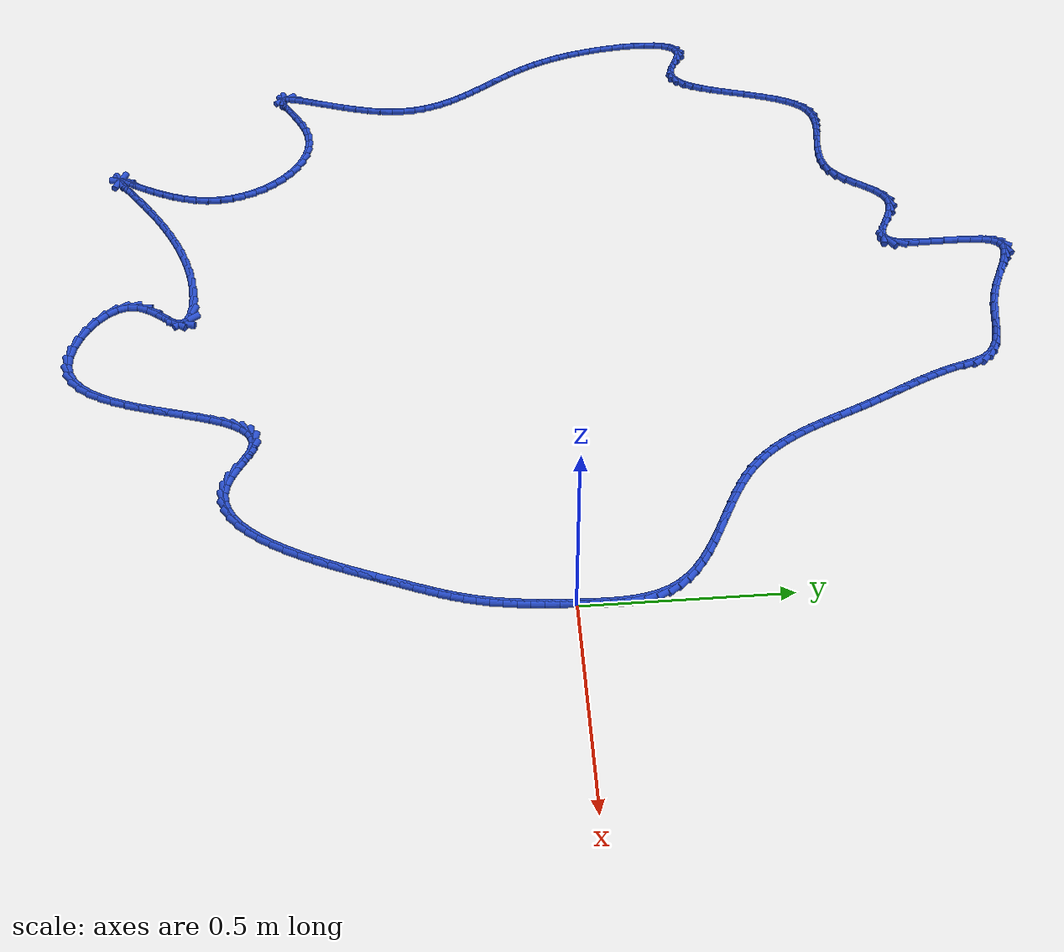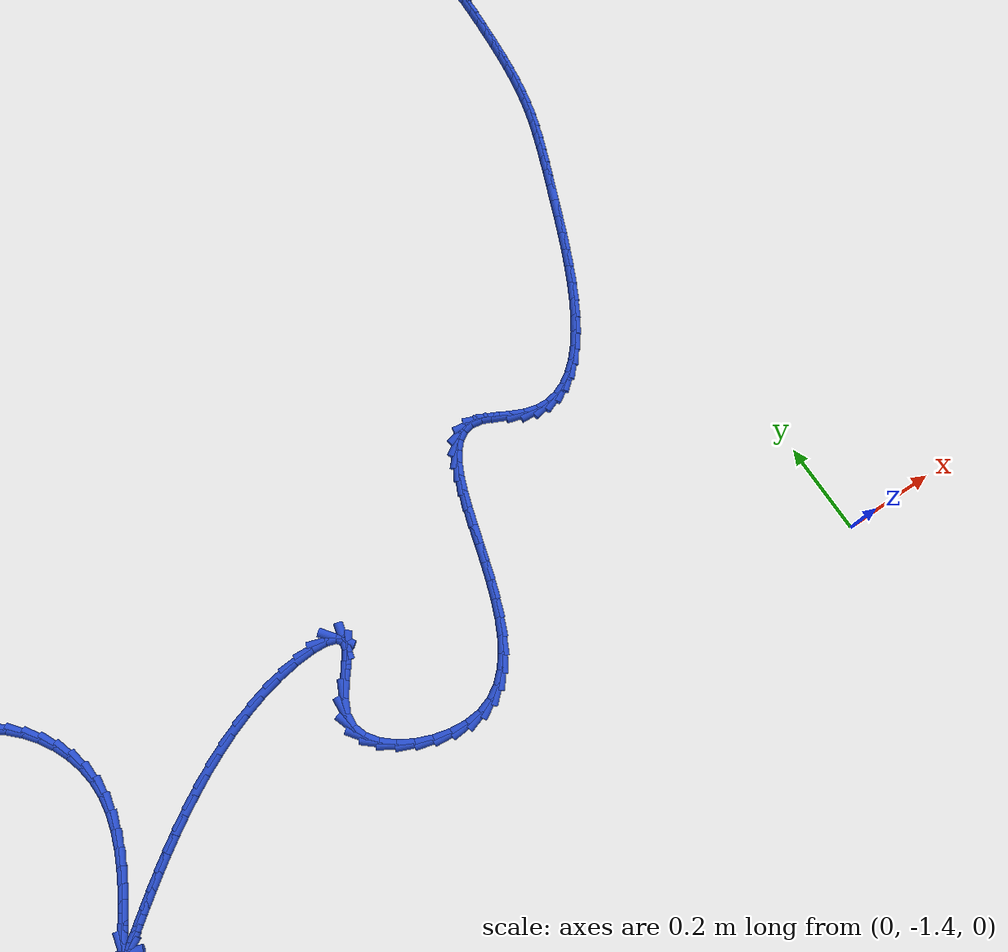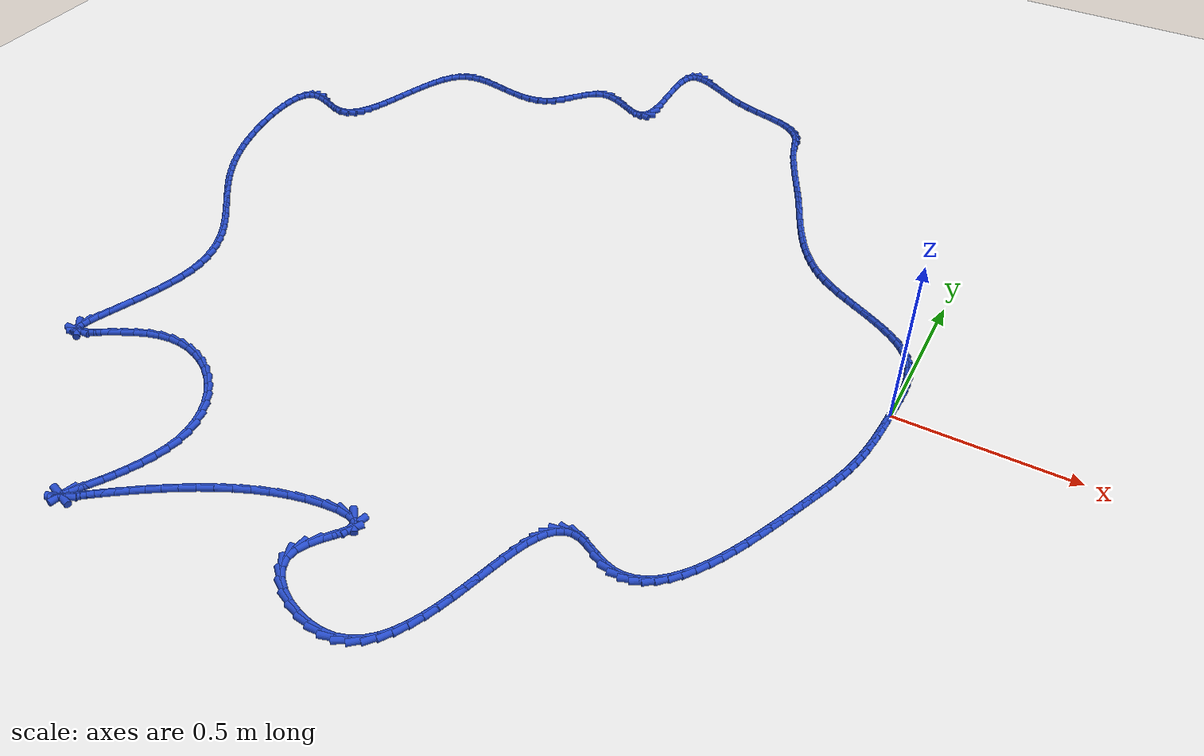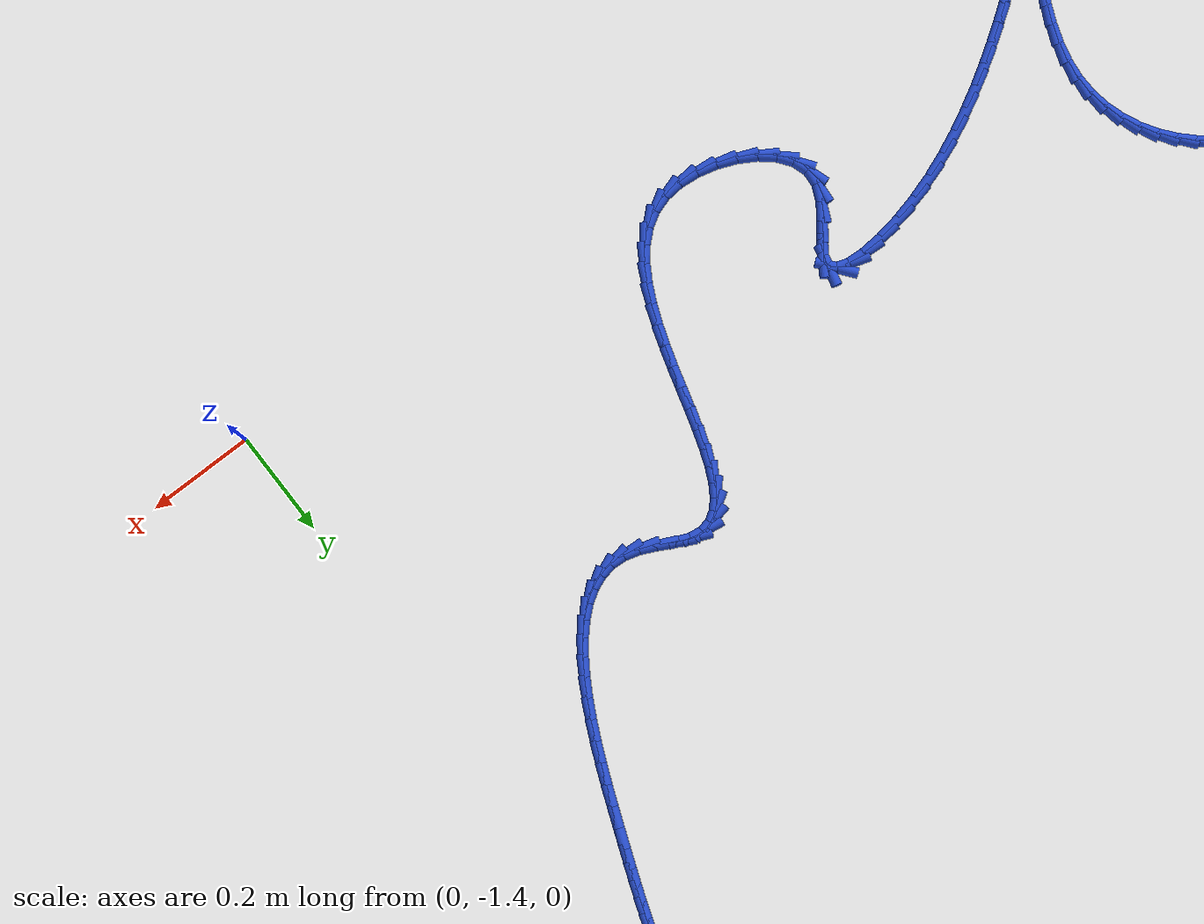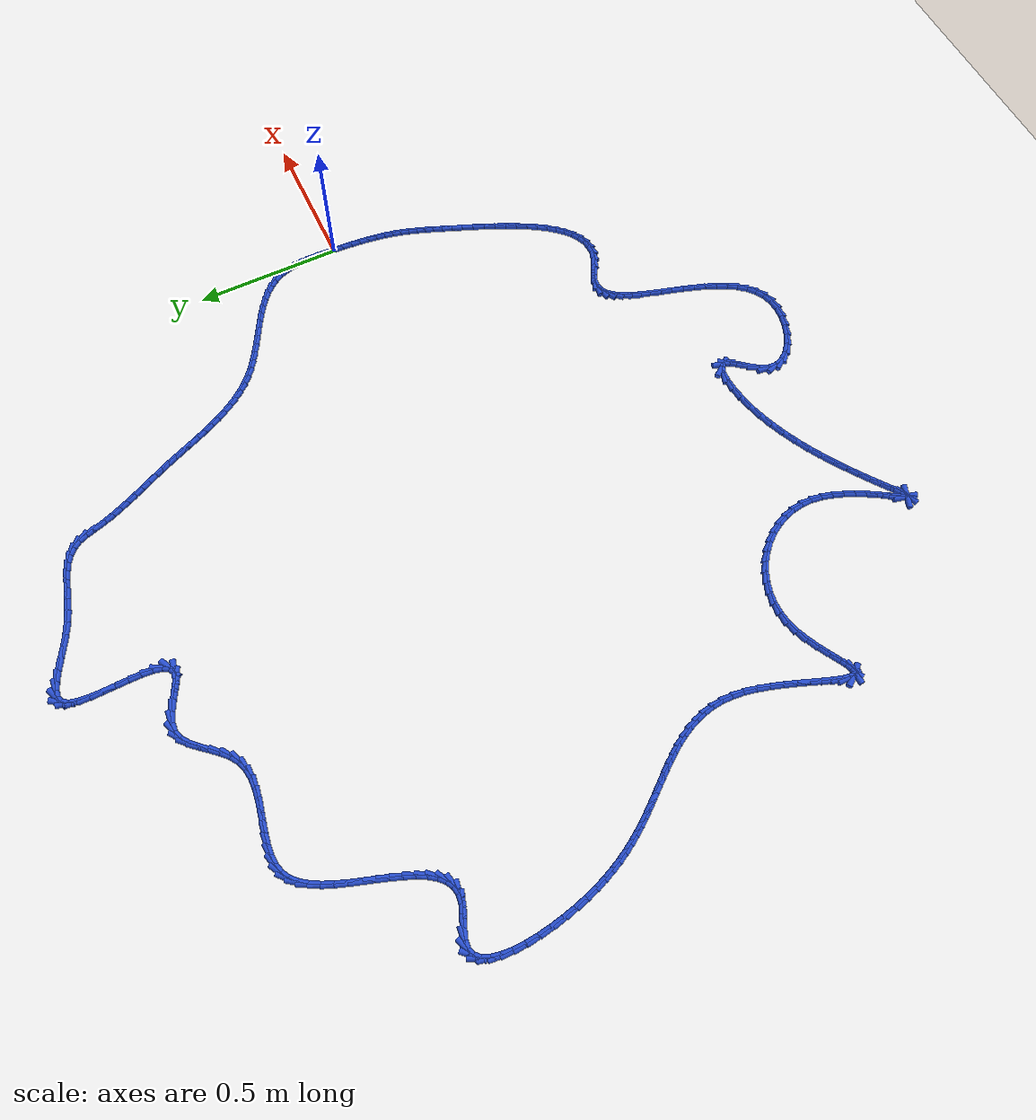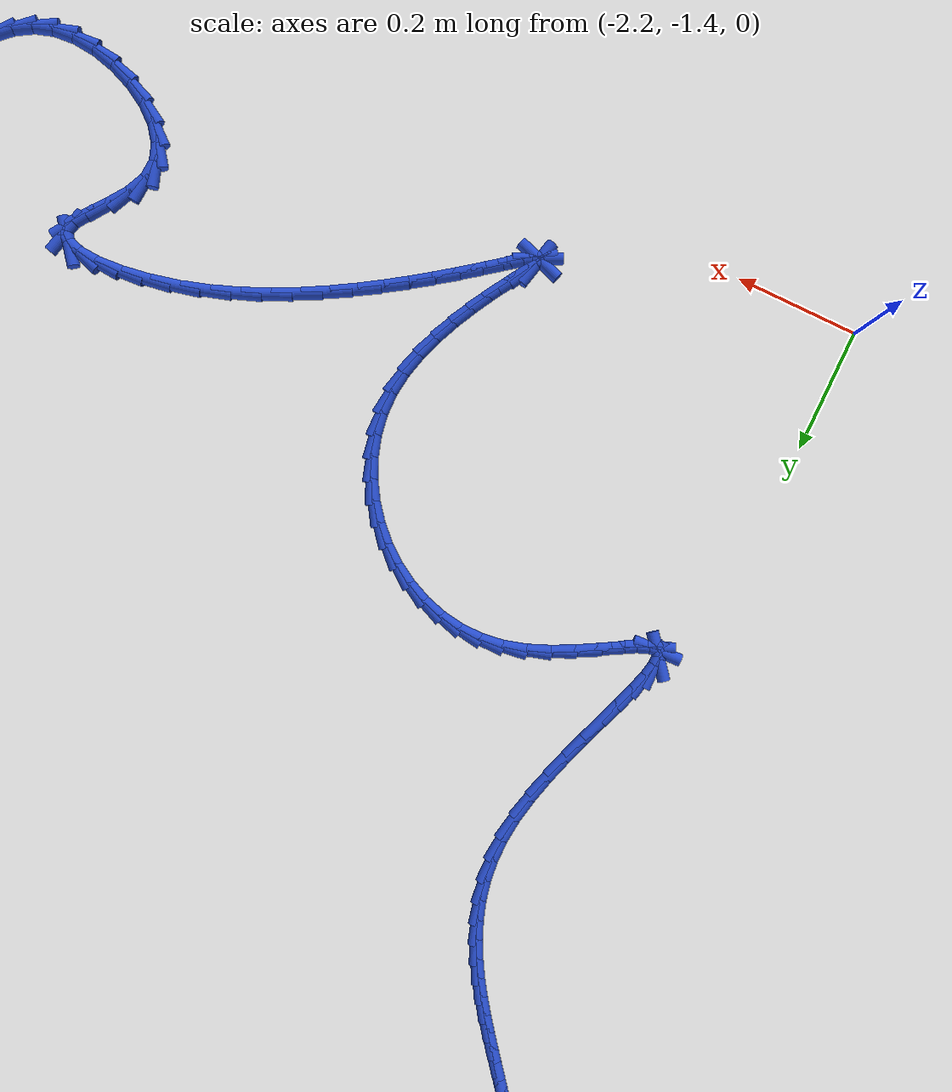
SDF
<sdf version="1.6">
 <world name="default">
  <light name="sun" type="directional">
   <pose>0 0 10 0 -0 0</pose>
   <diffuse>0.8 0.8 0.8 1</diffuse>
   <specular>0.2 0.2 0.2 1</specular>
   <attenuation>
    <range>1000</range>
    <constant>0.9</constant>
    <linear>0.01</linear>
    <quadratic>0.001</quadratic>
   </attenuation>
   <direction>-0.5 0.1 -0.9</direction>
  </light>
  <model name="ground_plane">
   <static>1</static>
   <link name="link">
    <collision name="collision">
     <geometry><plane><normal>0 0 1</normal><size>100 100</size></plane></geometry>
     <surface><friction><ode><mu>100</mu><mu2>50</mu2></ode></friction></surface>
    </collision>
    <visual name="visual">
     <cast_shadows>0</cast_shadows>
     <geometry><plane><normal>0 0 1</normal><size>100 100</size></plane></geometry>
     <material>
      <script><uri>file://media/materials/scripts/gazebo.material</uri><name>Gazebo/WhiteGlow</name></script>
     </material>
    </visual>
   </link>
  </model>
  <gravity>0 0 -9.8</gravity>
  <magnetic_field>6e-06 2.3e-05 -4.2e-05</magnetic_field>
  <atmosphere type="adiabatic"/>
  <physics name="default_physics" default="0" type="ode">
   <max_step_size>0.001</max_step_size>
   <real_time_factor>1</real_time_factor>
   <real_time_update_rate>1000</real_time_update_rate>
  </physics>
  <scene><ambient>0.4 0.4 0.4 1</ambient><background>0.7 0.7 0.7 1</background><shadows>1</shadows></scene>
  <spherical_coordinates>
   <surface_model>EARTH_WGS84</surface_model>
   <latitude_deg>0</latitude_deg>
   <longitude_deg>0</longitude_deg>
   <elevation>0</elevation>
   <heading_deg>0</heading_deg>
  </spherical_coordinates>
  <model name="line">
   <link name="link_0">
    <pose>-6.505213034913027e-19 3.469446951953614e-17 0.01 0 1.57 1.529829881621226</pose>
    <collision name="collision">
     <geometry><cylinder><radius>0.01</radius><length>0.08</length></cylinder></geometry>
    </collision>
    <visual name="visual">
     <material>
      <script><name>Gazebo/Blue</name><uri>file://media/materials/scripts/gazebo.material</uri></script>
     </material>
     <geometry><cylinder><radius>0.01</radius><length>0.08</length></cylinder></geometry>
    </visual>
   </link>
   <link name="link_1">
    <pose>0.0013395285515980372 0.03267989467079061 0.01 0 1.57 1.5513439483667566</pose>
    <collision name="collision">
     <geometry><cylinder><radius>0.01</radius><length>0.08</length></cylinder></geometry>
    </collision>
    <visual name="visual">
     <material>
      <script><name>Gazebo/Blue</name><uri>file://media/materials/scripts/gazebo.material</uri></script>
     </material>
     <geometry><cylinder><radius>0.01</radius><length>0.08</length></cylinder></geometry>
    </visual>
   </link>
   <link name="link_2">
    <pose>0.001975951728893649 0.06539275312661427 0.01 0 1.57 -1.5528110485071946</pose>
    <collision name="collision">
     <geometry><cylinder><radius>0.01</radius><length>0.08</length></cylinder></geometry>
    </collision>
    <visual name="visual">
     <material>
      <script><name>Gazebo/Blue</name><uri>file://media/materials/scripts/gazebo.material</uri></script>
     </material>
     <geometry><cylinder><radius>0.01</radius><length>0.08</length></cylinder></geometry>
    </visual>
   </link>
   <link name="link_3">
    <pose>0.0013943547094076732 0.09772665972823673 0.01 0 1.57 -1.4975506433726895</pose>
    <collision name="collision">
     <geometry><cylinder><radius>0.01</radius><length>0.08</length></cylinder></geometry>
    </collision>
    <visual name="visual">
     <material>
      <script><name>Gazebo/Blue</name><uri>file://media/materials/scripts/gazebo.material</uri></script>
     </material>
     <geometry><cylinder><radius>0.01</radius><length>0.08</length></cylinder></geometry>
    </visual>
   </link>
   <link name="link_4">
    <pose>-0.0009201773293390537 0.1292696988364237 0.01 0 1.57 -1.4215407506581588</pose>
    <collision name="collision">
     <geometry><cylinder><radius>0.01</radius><length>0.08</length></cylinder></geometry>
    </collision>
    <visual name="visual">
     <material>
      <script><name>Gazebo/Blue</name><uri>file://media/materials/scripts/gazebo.material</uri></script>
     </material>
     <geometry><cylinder><radius>0.01</radius><length>0.08</length></cylinder></geometry>
    </visual>
   </link>
   <link name="link_5">
    <pose>-0.005482559209825691 0.15960995481194085 0.01 0 1.57 -1.321113114206973</pose>
    <collision name="collision">
     <geometry><cylinder><radius>0.01</radius><length>0.08</length></cylinder></geometry>
    </collision>
    <visual name="visual">
     <material>
      <script><name>Gazebo/Blue</name><uri>file://media/materials/scripts/gazebo.material</uri></script>
     </material>
     <geometry><cylinder><radius>0.01</radius><length>0.08</length></cylinder></geometry>
    </visual>
   </link>
   <link name="link_6">
    <pose>-0.012807705754531409 0.1883355120155538 0.01 0 1.57 -1.1927705815434022</pose>
    <collision name="collision">
     <geometry><cylinder><radius>0.01</radius><length>0.08</length></cylinder></geometry>
    </collision>
    <visual name="visual">
     <material>
      <script><name>Gazebo/Blue</name><uri>file://media/materials/scripts/gazebo.material</uri></script>
     </material>
     <geometry><cylinder><radius>0.01</radius><length>0.08</length></cylinder></geometry>
    </visual>
   </link>
   <link name="link_7">
    <pose>-0.023410531783463372 0.21503445480988986 0.01 0 1.57 -1.042246012458625</pose>
    <collision name="collision">
     <geometry><cylinder><radius>0.01</radius><length>0.08</length></cylinder></geometry>
    </collision>
    <visual name="visual">
     <material>
      <script><name>Gazebo/Blue</name><uri>file://media/materials/scripts/gazebo.material</uri></script>
     </material>
     <geometry><cylinder><radius>0.01</radius><length>0.08</length></cylinder></geometry>
    </visual>
   </link>
   <link name="link_8">
    <pose>-0.037647566932659235 0.2394141376411778 0.01 0 1.57 -0.9013980884721358</pose>
    <collision name="collision">
     <geometry><cylinder><radius>0.01</radius><length>0.08</length></cylinder></geometry>
    </collision>
    <visual name="visual">
     <material>
      <script><name>Gazebo/Blue</name><uri>file://media/materials/scripts/gazebo.material</uri></script>
     </material>
     <geometry><cylinder><radius>0.01</radius><length>0.08</length></cylinder></geometry>
    </visual>
   </link>
   <link name="link_9">
    <pose>-0.05524654389775431 0.2616554230311535 0.01 0 1.57 -0.7821884065468719</pose>
    <collision name="collision">
     <geometry><cylinder><radius>0.01</radius><length>0.08</length></cylinder></geometry>
    </collision>
    <visual name="visual">
     <material>
      <script><name>Gazebo/Blue</name><uri>file://media/materials/scripts/gazebo.material</uri></script>
     </material>
     <geometry><cylinder><radius>0.01</radius><length>0.08</length></cylinder></geometry>
    </visual>
   </link>
   <link name="link_10">
    <pose>-0.07577917322147816 0.28205666413264835 0.01 0 1.57 -0.6859968358805981</pose>
    <collision name="collision">
     <geometry><cylinder><radius>0.01</radius><length>0.08</length></cylinder></geometry>
    </collision>
    <visual name="visual">
     <material>
      <script><name>Gazebo/Blue</name><uri>file://media/materials/scripts/gazebo.material</uri></script>
     </material>
     <geometry><cylinder><radius>0.01</radius><length>0.08</length></cylinder></geometry>
    </visual>
   </link>
   <link name="link_11">
    <pose>-0.09881716544656031 0.30091621409849406 0.01 0 1.57 -0.6116784188423741</pose>
    <collision name="collision">
     <geometry><cylinder><radius>0.01</radius><length>0.08</length></cylinder></geometry>
    </collision>
    <visual name="visual">
     <material>
      <script><name>Gazebo/Blue</name><uri>file://media/materials/scripts/gazebo.material</uri></script>
     </material>
     <geometry><cylinder><radius>0.01</radius><length>0.08</length></cylinder></geometry>
    </visual>
   </link>
   <link name="link_12">
    <pose>-0.12393223111573032 0.31853242608152205 0.01 0 1.57 -0.5570884559378451</pose>
    <collision name="collision">
     <geometry><cylinder><radius>0.01</radius><length>0.08</length></cylinder></geometry>
    </collision>
    <visual name="visual">
     <material>
      <script><name>Gazebo/Blue</name><uri>file://media/materials/scripts/gazebo.material</uri></script>
     </material>
     <geometry><cylinder><radius>0.01</radius><length>0.08</length></cylinder></geometry>
    </visual>
   </link>
   <link name="link_13">
    <pose>-0.15069608077171773 0.33520365323456364 0.01 0 1.57 -0.520049197506985</pose>
    <collision name="collision">
     <geometry><cylinder><radius>0.01</radius><length>0.08</length></cylinder></geometry>
    </collision>
    <visual name="visual">
     <material>
      <script><name>Gazebo/Blue</name><uri>file://media/materials/scripts/gazebo.material</uri></script>
     </material>
     <geometry><cylinder><radius>0.01</radius><length>0.08</length></cylinder></geometry>
    </visual>
   </link>
   <link name="link_14">
    <pose>-0.1786804249572521 0.3512282487104506 0.01 0 1.57 -0.49881138537012626</pose>
    <collision name="collision">
     <geometry><cylinder><radius>0.01</radius><length>0.08</length></cylinder></geometry>
    </collision>
    <visual name="visual">
     <material>
      <script><name>Gazebo/Blue</name><uri>file://media/materials/scripts/gazebo.material</uri></script>
     </material>
     <geometry><cylinder><radius>0.01</radius><length>0.08</length></cylinder></geometry>
    </visual>
   </link>
   <link name="link_15">
    <pose>-0.20745697421506293 0.3669045656620144 0.01 0 1.57 -0.4922204672798907</pose>
    <collision name="collision">
     <geometry><cylinder><radius>0.01</radius><length>0.08</length></cylinder></geometry>
    </collision>
    <visual name="visual">
     <material>
      <script><name>Gazebo/Blue</name><uri>file://media/materials/scripts/gazebo.material</uri></script>
     </material>
     <geometry><cylinder><radius>0.01</radius><length>0.08</length></cylinder></geometry>
    </visual>
   </link>
   <link name="link_16">
    <pose>-0.23659743908787975 0.3825309572420863 0.01 0 1.57 -0.4997477634314134</pose>
    <collision name="collision">
     <geometry><cylinder><radius>0.01</radius><length>0.08</length></cylinder></geometry>
    </collision>
    <visual name="visual">
     <material>
      <script><name>Gazebo/Blue</name><uri>file://media/materials/scripts/gazebo.material</uri></script>
     </material>
     <geometry><cylinder><radius>0.01</radius><length>0.08</length></cylinder></geometry>
    </visual>
   </link>
   <link name="link_17">
    <pose>-0.2656735301184322 0.39840577660349796 0.01 0 1.57 -0.5214695108505973</pose>
    <collision name="collision">
     <geometry><cylinder><radius>0.01</radius><length>0.08</length></cylinder></geometry>
    </collision>
    <visual name="visual">
     <material>
      <script><name>Gazebo/Blue</name><uri>file://media/materials/scripts/gazebo.material</uri></script>
     </material>
     <geometry><cylinder><radius>0.01</radius><length>0.08</length></cylinder></geometry>
    </visual>
   </link>
   <link name="link_18">
    <pose>-0.2942569578494497 0.4148273768990809 0.01 0 1.57 -0.558019080074125</pose>
    <collision name="collision">
     <geometry><cylinder><radius>0.01</radius><length>0.08</length></cylinder></geometry>
    </collision>
    <visual name="visual">
     <material>
      <script><name>Gazebo/Blue</name><uri>file://media/materials/scripts/gazebo.material</uri></script>
     </material>
     <geometry><cylinder><radius>0.01</radius><length>0.08</length></cylinder></geometry>
    </visual>
   </link>
   <link name="link_19">
    <pose>-0.32191943282366187 0.4320941112816665 0.01 0 1.57 -0.6104953210205936</pose>
    <collision name="collision">
     <geometry><cylinder><radius>0.01</radius><length>0.08</length></cylinder></geometry>
    </collision>
    <visual name="visual">
     <material>
      <script><name>Gazebo/Blue</name><uri>file://media/materials/scripts/gazebo.material</uri></script>
     </material>
     <geometry><cylinder><radius>0.01</radius><length>0.08</length></cylinder></geometry>
    </visual>
   </link>
   <link name="link_20">
    <pose>-0.34823266558379834 0.4505043329040864 0.01 0 1.57 -0.6802410978289483</pose>
    <collision name="collision">
     <geometry><cylinder><radius>0.01</radius><length>0.08</length></cylinder></geometry>
    </collision>
    <visual name="visual">
     <material>
      <script><name>Gazebo/Blue</name><uri>file://media/materials/scripts/gazebo.material</uri></script>
     </material>
     <geometry><cylinder><radius>0.01</radius><length>0.08</length></cylinder></geometry>
    </visual>
   </link>
   <link name="link_21">
    <pose>-0.37276914222797386 0.4703558199147374 0.01 0 1.57 -0.7616334286397187</pose>
    <collision name="collision">
     <geometry><cylinder><radius>0.01</radius><length>0.08</length></cylinder></geometry>
    </collision>
    <visual name="visual">
     <material>
      <script><name>Gazebo/Blue</name><uri>file://media/materials/scripts/gazebo.material</uri></script>
     </material>
     <geometry><cylinder><radius>0.01</radius><length>0.08</length></cylinder></geometry>
    </visual>
   </link>
   <link name="link_22">
    <pose>-0.395275577541639 0.4918171755896307 0.01 0 1.57 -0.8388582674073612</pose>
    <collision name="collision">
     <geometry><cylinder><radius>0.01</radius><length>0.08</length></cylinder></geometry>
    </collision>
    <visual name="visual">
     <material>
      <script><name>Gazebo/Blue</name><uri>file://media/materials/scripts/gazebo.material</uri></script>
     </material>
     <geometry><cylinder><radius>0.01</radius><length>0.08</length></cylinder></geometry>
    </visual>
   </link>
   <link name="link_23">
    <pose>-0.41589234574606965 0.5147651402046992 0.01 0 1.57 -0.9086278335481897</pose>
    <collision name="collision">
     <geometry><cylinder><radius>0.01</radius><length>0.08</length></cylinder></geometry>
    </collision>
    <visual name="visual">
     <material>
      <script><name>Gazebo/Blue</name><uri>file://media/materials/scripts/gazebo.material</uri></script>
     </material>
     <geometry><cylinder><radius>0.01</radius><length>0.08</length></cylinder></geometry>
    </visual>
   </link>
   <link name="link_24">
    <pose>-0.434813858648778 0.5390363900348619 0.01 0 1.57 -0.9702008232198723</pose>
    <collision name="collision">
     <geometry><cylinder><radius>0.01</radius><length>0.08</length></cylinder></geometry>
    </collision>
    <visual name="visual">
     <material>
      <script><name>Gazebo/Blue</name><uri>file://media/materials/scripts/gazebo.material</uri></script>
     </material>
     <geometry><cylinder><radius>0.01</radius><length>0.08</length></cylinder></geometry>
    </visual>
   </link>
   <link name="link_25">
    <pose>-0.45223452805727665 0.5644676013550373 0.01 0 1.57 -1.0232424873515744</pose>
    <collision name="collision">
     <geometry><cylinder><radius>0.01</radius><length>0.08</length></cylinder></geometry>
    </collision>
    <visual name="visual">
     <material>
      <script><name>Gazebo/Blue</name><uri>file://media/materials/scripts/gazebo.material</uri></script>
     </material>
     <geometry><cylinder><radius>0.01</radius><length>0.08</length></cylinder></geometry>
    </visual>
   </link>
   <link name="link_26">
    <pose>-0.46834876577907775 0.5908954504401436 0.01 0 1.57 -1.0677115628364142</pose>
    <collision name="collision">
     <geometry><cylinder><radius>0.01</radius><length>0.08</length></cylinder></geometry>
    </collision>
    <visual name="visual">
     <material>
      <script><name>Gazebo/Blue</name><uri>file://media/materials/scripts/gazebo.material</uri></script>
     </material>
     <geometry><cylinder><radius>0.01</radius><length>0.08</length></cylinder></geometry>
    </visual>
   </link>
   <link name="link_27">
    <pose>-0.4833509836216941 0.6181566135651002 0.01 0 1.57 -1.1037452056120285</pose>
    <collision name="collision">
     <geometry><cylinder><radius>0.01</radius><length>0.08</length></cylinder></geometry>
    </collision>
    <visual name="visual">
     <material>
      <script><name>Gazebo/Blue</name><uri>file://media/materials/scripts/gazebo.material</uri></script>
     </material>
     <geometry><cylinder><radius>0.01</radius><length>0.08</length></cylinder></geometry>
    </visual>
   </link>
   <link name="link_28">
    <pose>-0.4974355933926377 0.6460877670048252 0.01 0 1.57 -1.1315610788521993</pose>
    <collision name="collision">
     <geometry><cylinder><radius>0.01</radius><length>0.08</length></cylinder></geometry>
    </collision>
    <visual name="visual">
     <material>
      <script><name>Gazebo/Blue</name><uri>file://media/materials/scripts/gazebo.material</uri></script>
     </material>
     <geometry><cylinder><radius>0.01</radius><length>0.08</length></cylinder></geometry>
    </visual>
   </link>
   <link name="link_29">
    <pose>-0.5107970068994212 0.6745255870342374 0.01 0 1.57 -1.1513830278465342</pose>
    <collision name="collision">
     <geometry><cylinder><radius>0.01</radius><length>0.08</length></cylinder></geometry>
    </collision>
    <visual name="visual">
     <material>
      <script><name>Gazebo/Blue</name><uri>file://media/materials/scripts/gazebo.material</uri></script>
     </material>
     <geometry><cylinder><radius>0.01</radius><length>0.08</length></cylinder></geometry>
    </visual>
   </link>
   <link name="link_30">
    <pose>-0.5236296359495568 0.7033067499282553 0.01 0 1.57 -1.1633891805203649</pose>
    <collision name="collision">
     <geometry><cylinder><radius>0.01</radius><length>0.08</length></cylinder></geometry>
    </collision>
    <visual name="visual">
     <material>
      <script><name>Gazebo/Blue</name><uri>file://media/materials/scripts/gazebo.material</uri></script>
     </material>
     <geometry><cylinder><radius>0.01</radius><length>0.08</length></cylinder></geometry>
    </visual>
   </link>
   <link name="link_31">
    <pose>-0.5361278923505571 0.7322679319617976 0.01 0 1.57 -1.1676783106452504</pose>
    <collision name="collision">
     <geometry><cylinder><radius>0.01</radius><length>0.08</length></cylinder></geometry>
    </collision>
    <visual name="visual">
     <material>
      <script><name>Gazebo/Blue</name><uri>file://media/materials/scripts/gazebo.material</uri></script>
     </material>
     <geometry><cylinder><radius>0.01</radius><length>0.08</length></cylinder></geometry>
    </visual>
   </link>
   <link name="link_32">
    <pose>-0.5484861879099345 0.7612458094097831 0.01 0 1.57 -1.164250215678161</pose>
    <collision name="collision">
     <geometry><cylinder><radius>0.01</radius><length>0.08</length></cylinder></geometry>
    </collision>
    <visual name="visual">
     <material>
      <script><name>Gazebo/Blue</name><uri>file://media/materials/scripts/gazebo.material</uri></script>
     </material>
     <geometry><cylinder><radius>0.01</radius><length>0.08</length></cylinder></geometry>
    </visual>
   </link>
   <link name="link_33">
    <pose>-0.5608989344352014 0.7900770585471306 0.01 0 1.57 -1.15300546772476</pose>
    <collision name="collision">
     <geometry><cylinder><radius>0.01</radius><length>0.08</length></cylinder></geometry>
    </collision>
    <visual name="visual">
     <material>
      <script><name>Gazebo/Blue</name><uri>file://media/materials/scripts/gazebo.material</uri></script>
     </material>
     <geometry><cylinder><radius>0.01</radius><length>0.08</length></cylinder></geometry>
    </visual>
   </link>
   <link name="link_34">
    <pose>-0.5735603406411797 0.8185985280946925 0.01 0 1.57 -1.1373262863810127</pose>
    <collision name="collision">
     <geometry><cylinder><radius>0.01</radius><length>0.08</length></cylinder></geometry>
    </collision>
    <visual name="visual">
     <material>
      <script><name>Gazebo/Blue</name><uri>file://media/materials/scripts/gazebo.material</uri></script>
     </material>
     <geometry><cylinder><radius>0.01</radius><length>0.08</length></cylinder></geometry>
    </visual>
   </link>
   <link name="link_35">
    <pose>-0.5865765773410835 0.8467218197256773 0.01 0 1.57 -1.126359071277261</pose>
    <collision name="collision">
     <geometry><cylinder><radius>0.01</radius><length>0.08</length></cylinder></geometry>
    </collision>
    <visual name="visual">
     <material>
      <script><name>Gazebo/Blue</name><uri>file://media/materials/scripts/gazebo.material</uri></script>
     </material>
     <geometry><cylinder><radius>0.01</radius><length>0.08</length></cylinder></geometry>
    </visual>
   </link>
   <link name="link_36">
    <pose>-0.5998285972135813 0.8745497677548474 0.01 0 1.57 -1.1216978233604011</pose>
    <collision name="collision">
     <geometry><cylinder><radius>0.01</radius><length>0.08</length></cylinder></geometry>
    </collision>
    <visual name="visual">
     <material>
      <script><name>Gazebo/Blue</name><uri>file://media/materials/scripts/gazebo.material</uri></script>
     </material>
     <geometry><cylinder><radius>0.01</radius><length>0.08</length></cylinder></geometry>
    </visual>
   </link>
   <link name="link_37">
    <pose>-0.6131618508073494 0.9022153513434821 0.01 0 1.57 -1.1234362683984052</pose>
    <collision name="collision">
     <geometry><cylinder><radius>0.01</radius><length>0.08</length></cylinder></geometry>
    </collision>
    <visual name="visual">
     <material>
      <script><name>Gazebo/Blue</name><uri>file://media/materials/scripts/gazebo.material</uri></script>
     </material>
     <geometry><cylinder><radius>0.01</radius><length>0.08</length></cylinder></geometry>
    </visual>
   </link>
   <link name="link_38">
    <pose>-0.6264217886710648 0.9298515496528604 0.01 0 1.57 -1.1316016780983618</pose>
    <collision name="collision">
     <geometry><cylinder><radius>0.01</radius><length>0.08</length></cylinder></geometry>
    </collision>
    <visual name="visual">
     <material>
      <script><name>Gazebo/Blue</name><uri>file://media/materials/scripts/gazebo.material</uri></script>
     </material>
     <geometry><cylinder><radius>0.01</radius><length>0.08</length></cylinder></geometry>
    </visual>
   </link>
   <link name="link_39">
    <pose>-0.6394538613534049 0.9575913418442626 0.01 0 1.57 -1.1461516095344957</pose>
    <collision name="collision">
     <geometry><cylinder><radius>0.01</radius><length>0.08</length></cylinder></geometry>
    </collision>
    <visual name="visual">
     <material>
      <script><name>Gazebo/Blue</name><uri>file://media/materials/scripts/gazebo.material</uri></script>
     </material>
     <geometry><cylinder><radius>0.01</radius><length>0.08</length></cylinder></geometry>
    </visual>
   </link>
   <link name="link_40">
    <pose>-0.6521035194030462 0.9855677070789682 0.01 0 1.57 -1.1669647508998493</pose>
    <collision name="collision">
     <geometry><cylinder><radius>0.01</radius><length>0.08</length></cylinder></geometry>
    </collision>
    <visual name="visual">
     <material>
      <script><name>Gazebo/Blue</name><uri>file://media/materials/scripts/gazebo.material</uri></script>
     </material>
     <geometry><cylinder><radius>0.01</radius><length>0.08</length></cylinder></geometry>
    </visual>
   </link>
   <link name="link_41">
    <pose>-0.6642162133686661 1.013913624518257 0.01 0 1.57 -1.19382703794198</pose>
    <collision name="collision">
     <geometry><cylinder><radius>0.01</radius><length>0.08</length></cylinder></geometry>
    </collision>
    <visual name="visual">
     <material>
      <script><name>Gazebo/Blue</name><uri>file://media/materials/scripts/gazebo.material</uri></script>
     </material>
     <geometry><cylinder><radius>0.01</radius><length>0.08</length></cylinder></geometry>
    </visual>
   </link>
   <link name="link_42">
    <pose>-0.6756373937989412 1.042762073323408 0.01 0 1.57 -1.2264154750027942</pose>
    <collision name="collision">
     <geometry><cylinder><radius>0.01</radius><length>0.08</length></cylinder></geometry>
    </collision>
    <visual name="visual">
     <material>
      <script><name>Gazebo/Blue</name><uri>file://media/materials/scripts/gazebo.material</uri></script>
     </material>
     <geometry><cylinder><radius>0.01</radius><length>0.08</length></cylinder></geometry>
    </visual>
   </link>
   <link name="link_43">
    <pose>-0.6862125112425486 1.0722460326557008 0.01 0 1.57 -1.264243052041813</pose>
    <collision name="collision">
     <geometry><cylinder><radius>0.01</radius><length>0.08</length></cylinder></geometry>
    </collision>
    <visual name="visual">
     <material>
      <script><name>Gazebo/Blue</name><uri>file://media/materials/scripts/gazebo.material</uri></script>
     </material>
     <geometry><cylinder><radius>0.01</radius><length>0.08</length></cylinder></geometry>
    </visual>
   </link>
   <link name="link_44">
    <pose>-0.695788003755799 1.102497362797943 0.01 0 1.57 -1.277876940107387</pose>
    <collision name="collision">
     <geometry><cylinder><radius>0.01</radius><length>0.08</length></cylinder></geometry>
    </collision>
    <visual name="visual">
     <material>
      <script><name>Gazebo/Blue</name><uri>file://media/materials/scripts/gazebo.material</uri></script>
     </material>
     <geometry><cylinder><radius>0.01</radius><length>0.08</length></cylinder></geometry>
    </visual>
   </link>
   <link name="link_45">
    <pose>-0.7049351609405358 1.1328266435056273 0.01 0 1.57 -1.1804225111472426</pose>
    <collision name="collision">
     <geometry><cylinder><radius>0.01</radius><length>0.08</length></cylinder></geometry>
    </collision>
    <visual name="visual">
     <material>
      <script><name>Gazebo/Blue</name><uri>file://media/materials/scripts/gazebo.material</uri></script>
     </material>
     <geometry><cylinder><radius>0.01</radius><length>0.08</length></cylinder></geometry>
    </visual>
   </link>
   <link name="link_46">
    <pose>-0.7162294760239947 1.1602738749872568 0.01 0 1.57 -0.9624682290749637</pose>
    <collision name="collision">
     <geometry><cylinder><radius>0.01</radius><length>0.08</length></cylinder></geometry>
    </collision>
    <visual name="visual">
     <material>
      <script><name>Gazebo/Blue</name><uri>file://media/materials/scripts/gazebo.material</uri></script>
     </material>
     <geometry><cylinder><radius>0.01</radius><length>0.08</length></cylinder></geometry>
    </visual>
   </link>
   <link name="link_47">
    <pose>-0.7317511654336801 1.1825612822045959 0.01 0 1.57 -0.7318828029238305</pose>
    <collision name="collision">
     <geometry><cylinder><radius>0.01</radius><length>0.08</length></cylinder></geometry>
    </collision>
    <visual name="visual">
     <material>
      <script><name>Gazebo/Blue</name><uri>file://media/materials/scripts/gazebo.material</uri></script>
     </material>
     <geometry><cylinder><radius>0.01</radius><length>0.08</length></cylinder></geometry>
    </visual>
   </link>
   <link name="link_48">
    <pose>-0.7513926340298954 1.2002054875074784 0.01 0 1.57 -0.539981601670312</pose>
    <collision name="collision">
     <geometry><cylinder><radius>0.01</radius><length>0.08</length></cylinder></geometry>
    </collision>
    <visual name="visual">
     <material>
      <script><name>Gazebo/Blue</name><uri>file://media/materials/scripts/gazebo.material</uri></script>
     </material>
     <geometry><cylinder><radius>0.01</radius><length>0.08</length></cylinder></geometry>
    </visual>
   </link>
   <link name="link_49">
    <pose>-0.7746943410497866 1.2141726382161913 0.01 0 1.57 -0.4016380040006696</pose>
    <collision name="collision">
     <geometry><cylinder><radius>0.01</radius><length>0.08</length></cylinder></geometry>
    </collision>
    <visual name="visual">
     <material>
      <script><name>Gazebo/Blue</name><uri>file://media/materials/scripts/gazebo.material</uri></script>
     </material>
     <geometry><cylinder><radius>0.01</radius><length>0.08</length></cylinder></geometry>
    </visual>
   </link>
   <link name="link_50">
    <pose>-0.8011967457304994 1.2254288816510188 0.01 0 1.57 -0.31445846518207354</pose>
    <collision name="collision">
     <geometry><cylinder><radius>0.01</radius><length>0.08</length></cylinder></geometry>
    </collision>
    <visual name="visual">
     <material>
      <script><name>Gazebo/Blue</name><uri>file://media/materials/scripts/gazebo.material</uri></script>
     </material>
     <geometry><cylinder><radius>0.01</radius><length>0.08</length></cylinder></geometry>
    </visual>
   </link>
   <link name="link_51">
    <pose>-0.8304403073091797 1.2349403651322473 0.01 0 1.57 -0.27023632708271983</pose>
    <collision name="collision">
     <geometry><cylinder><radius>0.01</radius><length>0.08</length></cylinder></geometry>
    </collision>
    <visual name="visual">
     <material>
      <script><name>Gazebo/Blue</name><uri>file://media/materials/scripts/gazebo.material</uri></script>
     </material>
     <geometry><cylinder><radius>0.01</radius><length>0.08</length></cylinder></geometry>
    </visual>
   </link>
   <link name="link_52">
    <pose>-0.8619654850229735 1.2436732359801619 0.01 0 1.57 -0.2613806676420537</pose>
    <collision name="collision">
     <geometry><cylinder><radius>0.01</radius><length>0.08</length></cylinder></geometry>
    </collision>
    <visual name="visual">
     <material>
      <script><name>Gazebo/Blue</name><uri>file://media/materials/scripts/gazebo.material</uri></script>
     </material>
     <geometry><cylinder><radius>0.01</radius><length>0.08</length></cylinder></geometry>
    </visual>
   </link>
   <link name="link_53">
    <pose>-0.8953127381090266 1.252593641515048 0.01 0 1.57 -0.282476630890794</pose>
    <collision name="collision">
     <geometry><cylinder><radius>0.01</radius><length>0.08</length></cylinder></geometry>
    </collision>
    <visual name="visual">
     <material>
      <script><name>Gazebo/Blue</name><uri>file://media/materials/scripts/gazebo.material</uri></script>
     </material>
     <geometry><cylinder><radius>0.01</radius><length>0.08</length></cylinder></geometry>
    </visual>
   </link>
   <link name="link_54">
    <pose>-0.9300225258044843 1.262667729057191 0.01 0 1.57 -0.3298907648950737</pose>
    <collision name="collision">
     <geometry><cylinder><radius>0.01</radius><length>0.08</length></cylinder></geometry>
    </collision>
    <visual name="visual">
     <material>
      <script><name>Gazebo/Blue</name><uri>file://media/materials/scripts/gazebo.material</uri></script>
     </material>
     <geometry><cylinder><radius>0.01</radius><length>0.08</length></cylinder></geometry>
    </visual>
   </link>
   <link name="link_55">
    <pose>-0.9656353073464934 1.274861645926877 0.01 0 1.57 -0.40020855072597794</pose>
    <collision name="collision">
     <geometry><cylinder><radius>0.01</radius><length>0.08</length></cylinder></geometry>
    </collision>
    <visual name="visual">
     <material>
      <script><name>Gazebo/Blue</name><uri>file://media/materials/scripts/gazebo.material</uri></script>
     </material>
     <geometry><cylinder><radius>0.01</radius><length>0.08</length></cylinder></geometry>
    </visual>
   </link>
   <link name="link_56">
    <pose>-1.0016879356569826 1.2901133162944067 0.01 0 1.57 -0.4657508349254639</pose>
    <collision name="collision">
     <geometry><cylinder><radius>0.01</radius><length>0.08</length></cylinder></geometry>
    </collision>
    <visual name="visual">
     <material>
      <script><name>Gazebo/Blue</name><uri>file://media/materials/scripts/gazebo.material</uri></script>
     </material>
     <geometry><cylinder><radius>0.01</radius><length>0.08</length></cylinder></geometry>
    </visual>
   </link>
   <link name="link_57">
    <pose>-1.0375618902829367 1.308144706821995 0.01 0 1.57 -0.496324210705304</pose>
    <collision name="collision">
     <geometry><cylinder><radius>0.01</radius><length>0.08</length></cylinder></geometry>
    </collision>
    <visual name="visual">
     <material>
      <script><name>Gazebo/Blue</name><uri>file://media/materials/scripts/gazebo.material</uri></script>
     </material>
     <geometry><cylinder><radius>0.01</radius><length>0.08</length></cylinder></geometry>
    </visual>
   </link>
   <link name="link_58">
    <pose>-1.0724275674105406 1.3270258383510802 0.01 0 1.57 -0.4917506383574382</pose>
    <collision name="collision">
     <geometry><cylinder><radius>0.01</radius><length>0.08</length></cylinder></geometry>
    </collision>
    <visual name="visual">
     <material>
      <script><name>Gazebo/Blue</name><uri>file://media/materials/scripts/gazebo.material</uri></script>
     </material>
     <geometry><cylinder><radius>0.01</radius><length>0.08</length></cylinder></geometry>
    </visual>
   </link>
   <link name="link_59">
    <pose>-1.1054402859281611 1.3447087362590178 0.01 0 1.57 -0.44444442808521467</pose>
    <collision name="collision">
     <geometry><cylinder><radius>0.01</radius><length>0.08</length></cylinder></geometry>
    </collision>
    <visual name="visual">
     <material>
      <script><name>Gazebo/Blue</name><uri>file://media/materials/scripts/gazebo.material</uri></script>
     </material>
     <geometry><cylinder><radius>0.01</radius><length>0.08</length></cylinder></geometry>
    </visual>
   </link>
   <link name="link_60">
    <pose>-1.1357553647241658 1.3591454259231626 0.01 0 1.57 -0.3290694122734987</pose>
    <collision name="collision">
     <geometry><cylinder><radius>0.01</radius><length>0.08</length></cylinder></geometry>
    </collision>
    <visual name="visual">
     <material>
      <script><name>Gazebo/Blue</name><uri>file://media/materials/scripts/gazebo.material</uri></script>
     </material>
     <geometry><cylinder><radius>0.01</radius><length>0.08</length></cylinder></geometry>
    </visual>
   </link>
   <link name="link_61">
    <pose>-1.1625281226869217 1.3682879327208701 0.01 0 1.57 -0.08025115382690062</pose>
    <collision name="collision">
     <geometry><cylinder><radius>0.01</radius><length>0.08</length></cylinder></geometry>
    </collision>
    <visual name="visual">
     <material>
      <script><name>Gazebo/Blue</name><uri>file://media/materials/scripts/gazebo.material</uri></script>
     </material>
     <geometry><cylinder><radius>0.01</radius><length>0.08</length></cylinder></geometry>
    </visual>
   </link>
   <link name="link_62">
    <pose>-1.184913878704796 1.3700882820294964 0.01 0 1.57 0.416555840489086</pose>
    <collision name="collision">
     <geometry><cylinder><radius>0.01</radius><length>0.08</length></cylinder></geometry>
    </collision>
    <visual name="visual">
     <material>
      <script><name>Gazebo/Blue</name><uri>file://media/materials/scripts/gazebo.material</uri></script>
     </material>
     <geometry><cylinder><radius>0.01</radius><length>0.08</length></cylinder></geometry>
    </visual>
   </link>
   <link name="link_63">
    <pose>-1.2020679516661559 1.3624984992263964 0.01 0 1.57 1.0133230450220734</pose>
    <collision name="collision">
     <geometry><cylinder><radius>0.01</radius><length>0.08</length></cylinder></geometry>
    </collision>
    <visual name="visual">
     <material>
      <script><name>Gazebo/Blue</name><uri>file://media/materials/scripts/gazebo.material</uri></script>
     </material>
     <geometry><cylinder><radius>0.01</radius><length>0.08</length></cylinder></geometry>
    </visual>
   </link>
   <link name="link_64">
    <pose>-1.2134846195698843 1.344185982195421 0.01 0 1.57 1.3373936952782557</pose>
    <collision name="collision">
     <geometry><cylinder><radius>0.01</radius><length>0.08</length></cylinder></geometry>
    </collision>
    <visual name="visual">
     <material>
      <script><name>Gazebo/Blue</name><uri>file://media/materials/scripts/gazebo.material</uri></script>
     </material>
     <geometry><cylinder><radius>0.01</radius><length>0.08</length></cylinder></geometry>
    </visual>
   </link>
   <link name="link_65">
    <pose>-1.220020562138749 1.3166934748602017 0.01 0 1.57 1.4880343592978684</pose>
    <collision name="collision">
     <geometry><cylinder><radius>0.01</radius><length>0.08</length></cylinder></geometry>
    </collision>
    <visual name="visual">
     <material>
      <script><name>Gazebo/Blue</name><uri>file://media/materials/scripts/gazebo.material</uri></script>
     </material>
     <geometry><cylinder><radius>0.01</radius><length>0.08</length></cylinder></geometry>
    </visual>
   </link>
   <link name="link_66">
    <pose>-1.2228747087867788 1.2822860384147692 0.01 0 1.57 1.561290577081569</pose>
    <collision name="collision">
     <geometry><cylinder><radius>0.01</radius><length>0.08</length></cylinder></geometry>
    </collision>
    <visual name="visual">
     <material>
      <script><name>Gazebo/Blue</name><uri>file://media/materials/scripts/gazebo.material</uri></script>
     </material>
     <geometry><cylinder><radius>0.01</radius><length>0.08</length></cylinder></geometry>
    </visual>
   </link>
   <link name="link_67">
    <pose>-1.223245988929425 1.2432287340561563 0.01 0 1.57 -1.548777432876308</pose>
    <collision name="collision">
     <geometry><cylinder><radius>0.01</radius><length>0.08</length></cylinder></geometry>
    </collision>
    <visual name="visual">
     <material>
      <script><name>Gazebo/Blue</name><uri>file://media/materials/scripts/gazebo.material</uri></script>
     </material>
     <geometry><cylinder><radius>0.01</radius><length>0.08</length></cylinder></geometry>
    </visual>
   </link>
   <link name="link_68">
    <pose>-1.2223333319821366 1.201786622981392 0.01 0 1.57 -1.546796603275145</pose>
    <collision name="collision">
     <geometry><cylinder><radius>0.01</radius><length>0.08</length></cylinder></geometry>
    </collision>
    <visual name="visual">
     <material>
      <script><name>Gazebo/Blue</name><uri>file://media/materials/scripts/gazebo.material</uri></script>
     </material>
     <geometry><cylinder><radius>0.01</radius><length>0.08</length></cylinder></geometry>
    </visual>
   </link>
   <link name="link_69">
    <pose>-1.2213356673603661 1.1602247663875105 0.01 0 1.57 1.5678468852817549</pose>
    <collision name="collision">
     <geometry><cylinder><radius>0.01</radius><length>0.08</length></cylinder></geometry>
    </collision>
    <visual name="visual">
     <material>
      <script><name>Gazebo/Blue</name><uri>file://media/materials/scripts/gazebo.material</uri></script>
     </material>
     <geometry><cylinder><radius>0.01</radius><length>0.08</length></cylinder></geometry>
    </visual>
   </link>
   <link name="link_70">
    <pose>-1.2214519244795632 1.1208082254715424 0.01 0 1.57 1.5015165078537378</pose>
    <collision name="collision">
     <geometry><cylinder><radius>0.01</radius><length>0.08</length></cylinder></geometry>
    </collision>
    <visual name="visual">
     <material>
      <script><name>Gazebo/Blue</name><uri>file://media/materials/scripts/gazebo.material</uri></script>
     </material>
     <geometry><cylinder><radius>0.01</radius><length>0.08</length></cylinder></geometry>
    </visual>
   </link>
   <link name="link_71">
    <pose>-1.2238810327551783 1.0858020614305184 0.01 0 1.57 1.364093655709291</pose>
    <collision name="collision">
     <geometry><cylinder><radius>0.01</radius><length>0.08</length></cylinder></geometry>
    </collision>
    <visual name="visual">
     <material>
      <script><name>Gazebo/Blue</name><uri>file://media/materials/scripts/gazebo.material</uri></script>
     </material>
     <geometry><cylinder><radius>0.01</radius><length>0.08</length></cylinder></geometry>
    </visual>
   </link>
   <link name="link_72">
    <pose>-1.2298219216026625 1.0574713354614709 0.01 0 1.57 1.0684690195581639</pose>
    <collision name="collision">
     <geometry><cylinder><radius>0.01</radius><length>0.08</length></cylinder></geometry>
    </collision>
    <visual name="visual">
     <material>
      <script><name>Gazebo/Blue</name><uri>file://media/materials/scripts/gazebo.material</uri></script>
     </material>
     <geometry><cylinder><radius>0.01</radius><length>0.08</length></cylinder></geometry>
    </visual>
   </link>
   <link name="link_73">
    <pose>-1.2404735204374666 1.0380811087614317 0.01 0 1.57 0.45909057942380627</pose>
    <collision name="collision">
     <geometry><cylinder><radius>0.01</radius><length>0.08</length></cylinder></geometry>
    </collision>
    <visual name="visual">
     <material>
      <script><name>Gazebo/Blue</name><uri>file://media/materials/scripts/gazebo.material</uri></script>
     </material>
     <geometry><cylinder><radius>0.01</radius><length>0.08</length></cylinder></geometry>
    </visual>
   </link>
   <link name="link_74">
    <pose>-1.257034079914465 1.0298949489200555 0.01 0 1.57 -0.16240714039818074</pose>
    <collision name="collision">
     <geometry><cylinder><radius>0.01</radius><length>0.08</length></cylinder></geometry>
    </collision>
    <visual name="visual">
     <material>
      <script><name>Gazebo/Blue</name><uri>file://media/materials/scripts/gazebo.material</uri></script>
     </material>
     <geometry><cylinder><radius>0.01</radius><length>0.08</length></cylinder></geometry>
    </visual>
   </link>
   <link name="link_75">
    <pose>-1.2800127240141546 1.033660005630754 0.01 0 1.57 -0.408703517402526</pose>
    <collision name="collision">
     <geometry><cylinder><radius>0.01</radius><length>0.08</length></cylinder></geometry>
    </collision>
    <visual name="visual">
     <material>
      <script><name>Gazebo/Blue</name><uri>file://media/materials/scripts/gazebo.material</uri></script>
     </material>
     <geometry><cylinder><radius>0.01</radius><length>0.08</length></cylinder></geometry>
    </visual>
   </link>
   <link name="link_76">
    <pose>-1.3079317747277828 1.0457514862361301 0.01 0 1.57 -0.47638041289368177</pose>
    <collision name="collision">
     <geometry><cylinder><radius>0.01</radius><length>0.08</length></cylinder></geometry>
    </collision>
    <visual name="visual">
     <material>
      <script><name>Gazebo/Blue</name><uri>file://media/materials/scripts/gazebo.material</uri></script>
     </material>
     <geometry><cylinder><radius>0.01</radius><length>0.08</length></cylinder></geometry>
    </visual>
   </link>
   <link name="link_77">
    <pose>-1.3389576433630275 1.0617614193830587 0.01 0 1.57 -0.44794381986096843</pose>
    <collision name="collision">
     <geometry><cylinder><radius>0.01</radius><length>0.08</length></cylinder></geometry>
    </collision>
    <visual name="visual">
     <material>
      <script><name>Gazebo/Blue</name><uri>file://media/materials/scripts/gazebo.material</uri></script>
     </material>
     <geometry><cylinder><radius>0.01</radius><length>0.08</length></cylinder></geometry>
    </visual>
   </link>
   <link name="link_78">
    <pose>-1.3712567412275654 1.0772818337184131 0.01 0 1.57 -0.3229791551373206</pose>
    <collision name="collision">
     <geometry><cylinder><radius>0.01</radius><length>0.08</length></cylinder></geometry>
    </collision>
    <visual name="visual">
     <material>
      <script><name>Gazebo/Blue</name><uri>file://media/materials/scripts/gazebo.material</uri></script>
     </material>
     <geometry><cylinder><radius>0.01</radius><length>0.08</length></cylinder></geometry>
    </visual>
   </link>
   <link name="link_79">
    <pose>-1.402995479629073 1.0879047578890677 0.01 0 1.57 -0.04675832456952598</pose>
    <collision name="collision">
     <geometry><cylinder><radius>0.01</radius><length>0.08</length></cylinder></geometry>
    </collision>
    <visual name="visual">
     <material>
      <script><name>Gazebo/Blue</name><uri>file://media/materials/scripts/gazebo.material</uri></script>
     </material>
     <geometry><cylinder><radius>0.01</radius><length>0.08</length></cylinder></geometry>
    </visual>
   </link>
   <link name="link_80">
    <pose>-1.4323617937930946 1.089278879116643 0.01 0 1.57 0.3445039280822161</pose>
    <collision name="collision">
     <geometry><cylinder><radius>0.01</radius><length>0.08</length></cylinder></geometry>
    </collision>
    <visual name="visual">
     <material>
      <script><name>Gazebo/Blue</name><uri>file://media/materials/scripts/gazebo.material</uri></script>
     </material>
     <geometry><cylinder><radius>0.01</radius><length>0.08</length></cylinder></geometry>
    </visual>
   </link>
   <link name="link_81">
    <pose>-1.4586102398171208 1.0798606085125695 0.01 0 1.57 0.6373655005078352</pose>
    <collision name="collision">
     <geometry><cylinder><radius>0.01</radius><length>0.08</length></cylinder></geometry>
    </collision>
    <visual name="visual">
     <material>
      <script><name>Gazebo/Blue</name><uri>file://media/materials/scripts/gazebo.material</uri></script>
     </material>
     <geometry><cylinder><radius>0.01</radius><length>0.08</length></cylinder></geometry>
    </visual>
   </link>
   <link name="link_82">
    <pose>-1.4825308954020096 1.0621483938692484 0.01 0 1.57 0.8005340210043411</pose>
    <collision name="collision">
     <geometry><cylinder><radius>0.01</radius><length>0.08</length></cylinder></geometry>
    </collision>
    <visual name="visual">
     <material>
      <script><name>Gazebo/Blue</name><uri>file://media/materials/scripts/gazebo.material</uri></script>
     </material>
     <geometry><cylinder><radius>0.01</radius><length>0.08</length></cylinder></geometry>
    </visual>
   </link>
   <link name="link_83">
    <pose>-1.5050330629984732 1.0389545247453804 0.01 0 1.57 0.866095043393773</pose>
    <collision name="collision">
     <geometry><cylinder><radius>0.01</radius><length>0.08</length></cylinder></geometry>
    </collision>
    <visual name="visual">
     <material>
      <script><name>Gazebo/Blue</name><uri>file://media/materials/scripts/gazebo.material</uri></script>
     </material>
     <geometry><cylinder><radius>0.01</radius><length>0.08</length></cylinder></geometry>
    </visual>
   </link>
   <link name="link_84">
    <pose>-1.5270260450572242 1.0130912906996676 0.01 0 1.57 0.8544417400924657</pose>
    <collision name="collision">
     <geometry><cylinder><radius>0.01</radius><length>0.08</length></cylinder></geometry>
    </collision>
    <visual name="visual">
     <material>
      <script><name>Gazebo/Blue</name><uri>file://media/materials/scripts/gazebo.material</uri></script>
     </material>
     <geometry><cylinder><radius>0.01</radius><length>0.08</length></cylinder></geometry>
    </visual>
   </link>
   <link name="link_85">
    <pose>-1.5494191440289757 0.987370981290812 0.01 0 1.57 0.7652272118134313</pose>
    <collision name="collision">
     <geometry><cylinder><radius>0.01</radius><length>0.08</length></cylinder></geometry>
    </collision>
    <visual name="visual">
     <material>
      <script><name>Gazebo/Blue</name><uri>file://media/materials/scripts/gazebo.material</uri></script>
     </material>
     <geometry><cylinder><radius>0.01</radius><length>0.08</length></cylinder></geometry>
    </visual>
   </link>
   <link name="link_86">
    <pose>-1.5731216623644404 0.964605886077514 0.01 0 1.57 0.5816234673836334</pose>
    <collision name="collision">
     <geometry><cylinder><radius>0.01</radius><length>0.08</length></cylinder></geometry>
    </collision>
    <visual name="visual">
     <material>
      <script><name>Gazebo/Blue</name><uri>file://media/materials/scripts/gazebo.material</uri></script>
     </material>
     <geometry><cylinder><radius>0.01</radius><length>0.08</length></cylinder></geometry>
    </visual>
   </link>
   <link name="link_87">
    <pose>-1.5990299824087575 0.9475713922110943 0.01 0 1.57 0.3428331946001086</pose>
    <collision name="collision">
     <geometry><cylinder><radius>0.01</radius><length>0.08</length></cylinder></geometry>
    </collision>
    <visual name="visual">
     <material>
      <script><name>Gazebo/Blue</name><uri>file://media/materials/scripts/gazebo.material</uri></script>
     </material>
     <geometry><cylinder><radius>0.01</radius><length>0.08</length></cylinder></geometry>
    </visual>
   </link>
   <link name="link_88">
    <pose>-1.6274721462605706 0.9374195933498345 0.01 0 1.57 0.1412925538189366</pose>
    <collision name="collision">
     <geometry><cylinder><radius>0.01</radius><length>0.08</length></cylinder></geometry>
    </collision>
    <visual name="visual">
     <material>
      <script><name>Gazebo/Blue</name><uri>file://media/materials/scripts/gazebo.material</uri></script>
     </material>
     <geometry><cylinder><radius>0.01</radius><length>0.08</length></cylinder></geometry>
    </visual>
   </link>
   <link name="link_89">
    <pose>-1.6579972280644315 0.9330776947705102 0.01 0 1.57 -0.007296426452191781</pose>
    <collision name="collision">
     <geometry><cylinder><radius>0.01</radius><length>0.08</length></cylinder></geometry>
    </collision>
    <visual name="visual">
     <material>
      <script><name>Gazebo/Blue</name><uri>file://media/materials/scripts/gazebo.material</uri></script>
     </material>
     <geometry><cylinder><radius>0.01</radius><length>0.08</length></cylinder></geometry>
    </visual>
   </link>
   <link name="link_90">
    <pose>-1.6900979395482538 0.9333119194074675 0.01 0 1.57 -0.1074135313287241</pose>
    <collision name="collision">
     <geometry><cylinder><radius>0.01</radius><length>0.08</length></cylinder></geometry>
    </collision>
    <visual name="visual">
     <material>
      <script><name>Gazebo/Blue</name><uri>file://media/materials/scripts/gazebo.material</uri></script>
     </material>
     <geometry><cylinder><radius>0.01</radius><length>0.08</length></cylinder></geometry>
    </visual>
   </link>
   <link name="link_91">
    <pose>-1.723266992439951 0.9368884901950526 0.01 0 1.57 -0.16697854482565277</pose>
    <collision name="collision">
     <geometry><cylinder><radius>0.01</radius><length>0.08</length></cylinder></geometry>
    </collision>
    <visual name="visual">
     <material>
      <script><name>Gazebo/Blue</name><uri>file://media/materials/scripts/gazebo.material</uri></script>
     </material>
     <geometry><cylinder><radius>0.01</radius><length>0.08</length></cylinder></geometry>
    </visual>
   </link>
   <link name="link_92">
    <pose>-1.7569970984674381 0.9425736300676124 0.01 0 1.57 -0.19178691433867923</pose>
    <collision name="collision">
     <geometry><cylinder><radius>0.01</radius><length>0.08</length></cylinder></geometry>
    </collision>
    <visual name="visual">
     <material>
      <script><name>Gazebo/Blue</name><uri>file://media/materials/scripts/gazebo.material</uri></script>
     </material>
     <geometry><cylinder><radius>0.01</radius><length>0.08</length></cylinder></geometry>
    </visual>
   </link>
   <link name="link_93">
    <pose>-1.7907809693586294 0.9491335619594933 0.01 0 1.57 -0.1839420635735535</pose>
    <collision name="collision">
     <geometry><cylinder><radius>0.01</radius><length>0.08</length></cylinder></geometry>
    </collision>
    <visual name="visual">
     <material>
      <script><name>Gazebo/Blue</name><uri>file://media/materials/scripts/gazebo.material</uri></script>
     </material>
     <geometry><cylinder><radius>0.01</radius><length>0.08</length></cylinder></geometry>
    </visual>
   </link>
   <link name="link_94">
    <pose>-1.8241113168414387 0.9553345088050417 0.01 0 1.57 -0.14141156534196972</pose>
    <collision name="collision">
     <geometry><cylinder><radius>0.01</radius><length>0.08</length></cylinder></geometry>
    </collision>
    <visual name="visual">
     <material>
      <script><name>Gazebo/Blue</name><uri>file://media/materials/scripts/gazebo.material</uri></script>
     </material>
     <geometry><cylinder><radius>0.01</radius><length>0.08</length></cylinder></geometry>
    </visual>
   </link>
   <link name="link_95">
    <pose>-1.8564808526437808 0.9599426935386042 0.01 0 1.57 -0.0575919940776218</pose>
    <collision name="collision">
     <geometry><cylinder><radius>0.01</radius><length>0.08</length></cylinder></geometry>
    </collision>
    <visual name="visual">
     <material>
      <script><name>Gazebo/Blue</name><uri>file://media/materials/scripts/gazebo.material</uri></script>
     </material>
     <geometry><cylinder><radius>0.01</radius><length>0.08</length></cylinder></geometry>
    </visual>
   </link>
   <link name="link_96">
    <pose>-1.8873822884935691 0.9617243390945267 0.01 0 1.57 0.0786133892449537</pose>
    <collision name="collision">
     <geometry><cylinder><radius>0.01</radius><length>0.08</length></cylinder></geometry>
    </collision>
    <visual name="visual">
     <material>
      <script><name>Gazebo/Blue</name><uri>file://media/materials/scripts/gazebo.material</uri></script>
     </material>
     <geometry><cylinder><radius>0.01</radius><length>0.08</length></cylinder></geometry>
    </visual>
   </link>
   <link name="link_97">
    <pose>-1.9163083361187185 0.9594456684071564 0.01 0 1.57 0.2789119248589607</pose>
    <collision name="collision">
     <geometry><cylinder><radius>0.01</radius><length>0.08</length></cylinder></geometry>
    </collision>
    <visual name="visual">
     <material>
      <script><name>Gazebo/Blue</name><uri>file://media/materials/scripts/gazebo.material</uri></script>
     </material>
     <geometry><cylinder><radius>0.01</radius><length>0.08</length></cylinder></geometry>
    </visual>
   </link>
   <link name="link_98">
    <pose>-1.9427517072471434 0.9518729044108397 0.01 0 1.57 0.5373531390044232</pose>
    <collision name="collision">
     <geometry><cylinder><radius>0.01</radius><length>0.08</length></cylinder></geometry>
    </collision>
    <visual name="visual">
     <material>
      <script><name>Gazebo/Blue</name><uri>file://media/materials/scripts/gazebo.material</uri></script>
     </material>
     <geometry><cylinder><radius>0.01</radius><length>0.08</length></cylinder></geometry>
    </visual>
   </link>
   <link name="link_99">
    <pose>-1.9662473087307182 0.9378733464509055 0.01 0 1.57 0.7779060273444917</pose>
    <collision name="collision">
     <geometry><cylinder><radius>0.01</radius><length>0.08</length></cylinder></geometry>
    </collision>
    <visual name="visual">
     <material>
      <script><name>Gazebo/Blue</name><uri>file://media/materials/scripts/gazebo.material</uri></script>
     </material>
     <geometry><cylinder><radius>0.01</radius><length>0.08</length></cylinder></geometry>
    </visual>
   </link>
   <link name="link_100">
    <pose>-1.9868551073892797 0.9175720500333507 0.01 0 1.57 0.9549015927686312</pose>
    <collision name="collision">
     <geometry><cylinder><radius>0.01</radius><length>0.08</length></cylinder></geometry>
    </collision>
    <visual name="visual">
     <material>
      <script><name>Gazebo/Blue</name><uri>file://media/materials/scripts/gazebo.material</uri></script>
     </material>
     <geometry><cylinder><radius>0.01</radius><length>0.08</length></cylinder></geometry>
    </visual>
   </link>
   <link name="link_101">
    <pose>-2.0049909758756352 0.8919466261461241 0.01 0 1.57 1.077980445230382</pose>
    <collision name="collision">
     <geometry><cylinder><radius>0.01</radius><length>0.08</length></cylinder></geometry>
    </collision>
    <visual name="visual">
     <material>
      <script><name>Gazebo/Blue</name><uri>file://media/materials/scripts/gazebo.material</uri></script>
     </material>
     <geometry><cylinder><radius>0.01</radius><length>0.08</length></cylinder></geometry>
    </visual>
   </link>
   <link name="link_102">
    <pose>-2.0210775393697764 0.8619908611346211 0.01 0 1.57 1.1610489321738466</pose>
    <collision name="collision">
     <geometry><cylinder><radius>0.01</radius><length>0.08</length></cylinder></geometry>
    </collision>
    <visual name="visual">
     <material>
      <script><name>Gazebo/Blue</name><uri>file://media/materials/scripts/gazebo.material</uri></script>
     </material>
     <geometry><cylinder><radius>0.01</radius><length>0.08</length></cylinder></geometry>
    </visual>
   </link>
   <link name="link_103">
    <pose>-2.0355374230516916 0.8286985413442381 0.01 0 1.57 1.2146688304536806</pose>
    <collision name="collision">
     <geometry><cylinder><radius>0.01</radius><length>0.08</length></cylinder></geometry>
    </collision>
    <visual name="visual">
     <material>
      <script><name>Gazebo/Blue</name><uri>file://media/materials/scripts/gazebo.material</uri></script>
     </material>
     <geometry><cylinder><radius>0.01</radius><length>0.08</length></cylinder></geometry>
    </visual>
   </link>
   <link name="link_104">
    <pose>-2.0487932521013725 0.7930634531203716 0.01 0 1.57 1.2454879769954914</pose>
    <collision name="collision">
     <geometry><cylinder><radius>0.01</radius><length>0.08</length></cylinder></geometry>
    </collision>
    <visual name="visual">
     <material>
      <script><name>Gazebo/Blue</name><uri>file://media/materials/scripts/gazebo.material</uri></script>
     </material>
     <geometry><cylinder><radius>0.01</radius><length>0.08</length></cylinder></geometry>
    </visual>
   </link>
   <link name="link_105">
    <pose>-2.0612676516988078 0.7560793828084175 0.01 0 1.57 1.2570408727023374</pose>
    <collision name="collision">
     <geometry><cylinder><radius>0.01</radius><length>0.08</length></cylinder></geometry>
    </collision>
    <visual name="visual">
     <material>
      <script><name>Gazebo/Blue</name><uri>file://media/materials/scripts/gazebo.material</uri></script>
     </material>
     <geometry><cylinder><radius>0.01</radius><length>0.08</length></cylinder></geometry>
    </visual>
   </link>
   <link name="link_106">
    <pose>-2.0733832470239886 0.7187401167537721 0.01 0 1.57 1.2503740741767173</pose>
    <collision name="collision">
     <geometry><cylinder><radius>0.01</radius><length>0.08</length></cylinder></geometry>
    </collision>
    <visual name="visual">
     <material>
      <script><name>Gazebo/Blue</name><uri>file://media/materials/scripts/gazebo.material</uri></script>
     </material>
     <geometry><cylinder><radius>0.01</radius><length>0.08</length></cylinder></geometry>
    </visual>
   </link>
   <link name="link_107">
    <pose>-2.085562663256905 0.6820394413018318 0.01 0 1.57 1.2241991888541486</pose>
    <collision name="collision">
     <geometry><cylinder><radius>0.01</radius><length>0.08</length></cylinder></geometry>
    </collision>
    <visual name="visual">
     <material>
      <script><name>Gazebo/Blue</name><uri>file://media/materials/scripts/gazebo.material</uri></script>
     </material>
     <geometry><cylinder><radius>0.01</radius><length>0.08</length></cylinder></geometry>
    </visual>
   </link>
   <link name="link_108">
    <pose>-2.098228525577547 0.6469711427979931 0.01 0 1.57 1.1744991787243295</pose>
    <collision name="collision">
     <geometry><cylinder><radius>0.01</radius><length>0.08</length></cylinder></geometry>
    </collision>
    <visual name="visual">
     <material>
      <script><name>Gazebo/Blue</name><uri>file://media/materials/scripts/gazebo.material</uri></script>
     </material>
     <geometry><cylinder><radius>0.01</radius><length>0.08</length></cylinder></geometry>
    </visual>
   </link>
   <link name="link_109">
    <pose>-2.1118034591659036 0.614529007587651 0.01 0 1.57 1.0934891838850425</pose>
    <collision name="collision">
     <geometry><cylinder><radius>0.01</radius><length>0.08</length></cylinder></geometry>
    </collision>
    <visual name="visual">
     <material>
      <script><name>Gazebo/Blue</name><uri>file://media/materials/scripts/gazebo.material</uri></script>
     </material>
     <geometry><cylinder><radius>0.01</radius><length>0.08</length></cylinder></geometry>
    </visual>
   </link>
   <link name="link_110">
    <pose>-2.1267100892019677 0.5857068220162028 0.01 0 1.57 0.968014276247881</pose>
    <collision name="collision">
     <geometry><cylinder><radius>0.01</radius><length>0.08</length></cylinder></geometry>
    </collision>
    <visual name="visual">
     <material>
      <script><name>Gazebo/Blue</name><uri>file://media/materials/scripts/gazebo.material</uri></script>
     </material>
     <geometry><cylinder><radius>0.01</radius><length>0.08</length></cylinder></geometry>
    </visual>
   </link>
   <link name="link_111">
    <pose>-2.1433710408657274 0.5614983724290442 0.01 0 1.57 0.7790686900547636</pose>
    <collision name="collision">
     <geometry><cylinder><radius>0.01</radius><length>0.08</length></cylinder></geometry>
    </collision>
    <visual name="visual">
     <material>
      <script><name>Gazebo/Blue</name><uri>file://media/materials/scripts/gazebo.material</uri></script>
     </material>
     <geometry><cylinder><radius>0.01</radius><length>0.08</length></cylinder></geometry>
    </visual>
   </link>
   <link name="link_112">
    <pose>-2.162208939337173 0.5428974451715716 0.01 0 1.57 0.5102977893418454</pose>
    <collision name="collision">
     <geometry><cylinder><radius>0.01</radius><length>0.08</length></cylinder></geometry>
    </collision>
    <visual name="visual">
     <material>
      <script><name>Gazebo/Blue</name><uri>file://media/materials/scripts/gazebo.material</uri></script>
     </material>
     <geometry><cylinder><radius>0.01</radius><length>0.08</length></cylinder></geometry>
    </visual>
   </link>
   <link name="link_113">
    <pose>-2.183646409796296 0.5308978265891812 0.01 0 1.57 0.17816356056038118</pose>
    <collision name="collision">
     <geometry><cylinder><radius>0.01</radius><length>0.08</length></cylinder></geometry>
    </collision>
    <visual name="visual">
     <material>
      <script><name>Gazebo/Blue</name><uri>file://media/materials/scripts/gazebo.material</uri></script>
     </material>
     <geometry><cylinder><radius>0.01</radius><length>0.08</length></cylinder></geometry>
    </visual>
   </link>
   <link name="link_114">
    <pose>-2.2081060774230847 0.526493303027269 0.01 0 1.57 -0.14560420886143113</pose>
    <collision name="collision">
     <geometry><cylinder><radius>0.01</radius><length>0.08</length></cylinder></geometry>
    </collision>
    <visual name="visual">
     <material>
      <script><name>Gazebo/Blue</name><uri>file://media/materials/scripts/gazebo.material</uri></script>
     </material>
     <geometry><cylinder><radius>0.01</radius><length>0.08</length></cylinder></geometry>
    </visual>
   </link>
   <link name="link_115">
    <pose>-2.2359653345367088 0.5305786395147972 0.01 0 1.57 -0.3411292893565607</pose>
    <collision name="collision">
     <geometry><cylinder><radius>0.01</radius><length>0.08</length></cylinder></geometry>
    </collision>
    <visual name="visual">
     <material>
      <script><name>Gazebo/Blue</name><uri>file://media/materials/scripts/gazebo.material</uri></script>
     </material>
     <geometry><cylinder><radius>0.01</radius><length>0.08</length></cylinder></geometry>
    </visual>
   </link>
   <link name="link_116">
    <pose>-2.2663809211932824 0.5413764155986981 0.01 0 1.57 -0.39446650848172865</pose>
    <collision name="collision">
     <geometry><cylinder><radius>0.01</radius><length>0.08</length></cylinder></geometry>
    </collision>
    <visual name="visual">
     <material>
      <script><name>Gazebo/Blue</name><uri>file://media/materials/scripts/gazebo.material</uri></script>
     </material>
     <geometry><cylinder><radius>0.01</radius><length>0.08</length></cylinder></geometry>
    </visual>
   </link>
   <link name="link_117">
    <pose>-2.297179470340588 0.554197412755318 0.01 0 1.57 -0.3329331459593168</pose>
    <collision name="collision">
     <geometry><cylinder><radius>0.01</radius><length>0.08</length></cylinder></geometry>
    </collision>
    <visual name="visual">
     <material>
      <script><name>Gazebo/Blue</name><uri>file://media/materials/scripts/gazebo.material</uri></script>
     </material>
     <geometry><cylinder><radius>0.01</radius><length>0.08</length></cylinder></geometry>
    </visual>
   </link>
   <link name="link_118">
    <pose>-2.3261204404783906 0.5642053578163735 0.01 0 1.57 -0.09780128690900203</pose>
    <collision name="collision">
     <geometry><cylinder><radius>0.01</radius><length>0.08</length></cylinder></geometry>
    </collision>
    <visual name="visual">
     <material>
      <script><name>Gazebo/Blue</name><uri>file://media/materials/scripts/gazebo.material</uri></script>
     </material>
     <geometry><cylinder><radius>0.01</radius><length>0.08</length></cylinder></geometry>
    </visual>
   </link>
   <link name="link_119">
    <pose>-2.3509991535097488 0.5666463155964815 0.01 0 1.57 0.3510439480519838</pose>
    <collision name="collision">
     <geometry><cylinder><radius>0.01</radius><length>0.08</length></cylinder></geometry>
    </collision>
    <visual name="visual">
     <material>
      <script><name>Gazebo/Blue</name><uri>file://media/materials/scripts/gazebo.material</uri></script>
     </material>
     <geometry><cylinder><radius>0.01</radius><length>0.08</length></cylinder></geometry>
    </visual>
   </link>
   <link name="link_120">
    <pose>-2.3707619476023707 0.5594089433251759 0.01 0 1.57 0.8153757313475437</pose>
    <collision name="collision">
     <geometry><cylinder><radius>0.01</radius><length>0.08</length></cylinder></geometry>
    </collision>
    <visual name="visual">
     <material>
      <script><name>Gazebo/Blue</name><uri>file://media/materials/scripts/gazebo.material</uri></script>
     </material>
     <geometry><cylinder><radius>0.01</radius><length>0.08</length></cylinder></geometry>
    </visual>
   </link>
   <link name="link_121">
    <pose>-2.3857231797135428 0.5435227018746578 0.01 0 1.57 1.145859691000147</pose>
    <collision name="collision">
     <geometry><cylinder><radius>0.01</radius><length>0.08</length></cylinder></geometry>
    </collision>
    <visual name="visual">
     <material>
      <script><name>Gazebo/Blue</name><uri>file://media/materials/scripts/gazebo.material</uri></script>
     </material>
     <geometry><cylinder><radius>0.01</radius><length>0.08</length></cylinder></geometry>
    </visual>
   </link>
   <link name="link_122">
    <pose>-2.3962768769739484 0.5201999650805552 0.01 0 1.57 1.3529589541764322</pose>
    <collision name="collision">
     <geometry><cylinder><radius>0.01</radius><length>0.08</length></cylinder></geometry>
    </collision>
    <visual name="visual">
     <material>
      <script><name>Gazebo/Blue</name><uri>file://media/materials/scripts/gazebo.material</uri></script>
     </material>
     <geometry><cylinder><radius>0.01</radius><length>0.08</length></cylinder></geometry>
    </visual>
   </link>
   <link name="link_123">
    <pose>-2.4028170665142703 0.49065310677849633 0.01 0 1.57 1.486482027183626</pose>
    <collision name="collision">
     <geometry><cylinder><radius>0.01</radius><length>0.08</length></cylinder></geometry>
    </collision>
    <visual name="visual">
     <material>
      <script><name>Gazebo/Blue</name><uri>file://media/materials/scripts/gazebo.material</uri></script>
     </material>
     <geometry><cylinder><radius>0.01</radius><length>0.08</length></cylinder></geometry>
    </visual>
   </link>
   <link name="link_124">
    <pose>-2.405737775465193 0.45609450080410996 0.01 0 1.57 -1.5628517453072714</pose>
    <collision name="collision">
     <geometry><cylinder><radius>0.01</radius><length>0.08</length></cylinder></geometry>
    </collision>
    <visual name="visual">
     <material>
      <script><name>Gazebo/Blue</name><uri>file://media/materials/scripts/gazebo.material</uri></script>
     </material>
     <geometry><cylinder><radius>0.01</radius><length>0.08</length></cylinder></geometry>
    </visual>
   </link>
   <link name="link_125">
    <pose>-2.4054330309574 0.41773652099302305 0.01 0 1.57 -1.494350830959944</pose>
    <collision name="collision">
     <geometry><cylinder><radius>0.01</radius><length>0.08</length></cylinder></geometry>
    </collision>
    <visual name="visual">
     <material>
      <script><name>Gazebo/Blue</name><uri>file://media/materials/scripts/gazebo.material</uri></script>
     </material>
     <geometry><cylinder><radius>0.01</radius><length>0.08</length></cylinder></geometry>
    </visual>
   </link>
   <link name="link_126">
    <pose>-2.4022968601215737 0.376791541180864 0.01 0 1.57 -1.4398481300997918</pose>
    <collision name="collision">
     <geometry><cylinder><radius>0.01</radius><length>0.08</length></cylinder></geometry>
    </collision>
    <visual name="visual">
     <material>
      <script><name>Gazebo/Blue</name><uri>file://media/materials/scripts/gazebo.material</uri></script>
     </material>
     <geometry><cylinder><radius>0.01</radius><length>0.08</length></cylinder></geometry>
    </visual>
   </link>
   <link name="link_127">
    <pose>-2.3967232900884 0.33447193520326124 0.01 0 1.57 -1.3933827594959565</pose>
    <collision name="collision">
     <geometry><cylinder><radius>0.01</radius><length>0.08</length></cylinder></geometry>
    </collision>
    <visual name="visual">
     <material>
      <script><name>Gazebo/Blue</name><uri>file://media/materials/scripts/gazebo.material</uri></script>
     </material>
     <geometry><cylinder><radius>0.01</radius><length>0.08</length></cylinder></geometry>
    </visual>
   </link>
   <link name="link_128">
    <pose>-2.3891063479885606 0.29199007689584267 0.01 0 1.57 -1.3507653865570508</pose>
    <collision name="collision">
     <geometry><cylinder><radius>0.01</radius><length>0.08</length></cylinder></geometry>
    </collision>
    <visual name="visual">
     <material>
      <script><name>Gazebo/Blue</name><uri>file://media/materials/scripts/gazebo.material</uri></script>
     </material>
     <geometry><cylinder><radius>0.01</radius><length>0.08</length></cylinder></geometry>
    </visual>
   </link>
   <link name="link_129">
    <pose>-2.37984006095274 0.2505583400942365 0.01 0 1.57 -1.3084088116859447</pose>
    <collision name="collision">
     <geometry><cylinder><radius>0.01</radius><length>0.08</length></cylinder></geometry>
    </collision>
    <visual name="visual">
     <material>
      <script><name>Gazebo/Blue</name><uri>file://media/materials/scripts/gazebo.material</uri></script>
     </material>
     <geometry><cylinder><radius>0.01</radius><length>0.08</length></cylinder></geometry>
    </visual>
   </link>
   <link name="link_130">
    <pose>-2.369311894583601 0.21135891983763846 0.01 0 1.57 -1.2640784018285764</pose>
    <collision name="collision">
     <geometry><cylinder><radius>0.01</radius><length>0.08</length></cylinder></geometry>
    </collision>
    <visual name="visual">
     <material>
      <script><name>Gazebo/Blue</name><uri>file://media/materials/scripts/gazebo.material</uri></script>
     </material>
     <geometry><cylinder><radius>0.01</radius><length>0.08</length></cylinder></geometry>
    </visual>
   </link>
   <link name="link_131">
    <pose>-2.357758103028605 0.17487853600904502 0.01 0 1.57 -1.218351418493731</pose>
    <collision name="collision">
     <geometry><cylinder><radius>0.01</radius><length>0.08</length></cylinder></geometry>
    </collision>
    <visual name="visual">
     <material>
      <script><name>Gazebo/Blue</name><uri>file://media/materials/scripts/gazebo.material</uri></script>
     </material>
     <geometry><cylinder><radius>0.01</radius><length>0.08</length></cylinder></geometry>
    </visual>
   </link>
   <link name="link_132">
    <pose>-2.34526356417951 0.1409076753592583 0.01 0 1.57 -1.1720290863942335</pose>
    <collision name="collision">
     <geometry><cylinder><radius>0.01</radius><length>0.08</length></cylinder></geometry>
    </collision>
    <visual name="visual">
     <material>
      <script><name>Gazebo/Blue</name><uri>file://media/materials/scripts/gazebo.material</uri></script>
     </material>
     <geometry><cylinder><radius>0.01</radius><length>0.08</length></cylinder></geometry>
    </visual>
   </link>
   <link name="link_133">
    <pose>-2.3319065614399426 0.1092064942473933 0.01 0 1.57 -1.126048284608498</pose>
    <collision name="collision">
     <geometry><cylinder><radius>0.01</radius><length>0.08</length></cylinder></geometry>
    </collision>
    <visual name="visual">
     <material>
      <script><name>Gazebo/Blue</name><uri>file://media/materials/scripts/gazebo.material</uri></script>
     </material>
     <geometry><cylinder><radius>0.01</radius><length>0.08</length></cylinder></geometry>
    </visual>
   </link>
   <link name="link_134">
    <pose>-2.317765378213529 0.07953514903256344 0.01 0 1.57 -1.0814807527635057</pose>
    <collision name="collision">
     <geometry><cylinder><radius>0.01</radius><length>0.08</length></cylinder></geometry>
    </collision>
    <visual name="visual">
     <material>
      <script><name>Gazebo/Blue</name><uri>file://media/materials/scripts/gazebo.material</uri></script>
     </material>
     <geometry><cylinder><radius>0.01</radius><length>0.08</length></cylinder></geometry>
    </visual>
   </link>
   <link name="link_135">
    <pose>-2.302918297903895 0.051653796073883665 0.01 0 1.57 -1.0394744087513288</pose>
    <collision name="collision">
     <geometry><cylinder><radius>0.01</radius><length>0.08</length></cylinder></geometry>
    </collision>
    <visual name="visual">
     <material>
      <script><name>Gazebo/Blue</name><uri>file://media/materials/scripts/gazebo.material</uri></script>
     </material>
     <geometry><cylinder><radius>0.01</radius><length>0.08</length></cylinder></geometry>
    </visual>
   </link>
   <link name="link_136">
    <pose>-2.2874436039146664 0.02532259173046843 0.01 0 1.57 -1.0011812708085372</pose>
    <collision name="collision">
     <geometry><cylinder><radius>0.01</radius><length>0.08</length></cylinder></geometry>
    </collision>
    <visual name="visual">
     <material>
      <script><name>Gazebo/Blue</name><uri>file://media/materials/scripts/gazebo.material</uri></script>
     </material>
     <geometry><cylinder><radius>0.01</radius><length>0.08</length></cylinder></geometry>
    </visual>
   </link>
   <link name="link_137">
    <pose>-2.2714195796494696 0.0003016923614322011 0.01 0 1.57 -0.9676831285415876</pose>
    <collision name="collision">
     <geometry><cylinder><radius>0.01</radius><length>0.08</length></cylinder></geometry>
    </collision>
    <visual name="visual">
     <material>
      <script><name>Gazebo/Blue</name><uri>file://media/materials/scripts/gazebo.material</uri></script>
     </material>
     <geometry><cylinder><radius>0.01</radius><length>0.08</length></cylinder></geometry>
    </visual>
   </link>
   <link name="link_138">
    <pose>-2.2549245085119303 -0.02364874567411056 0.01 0 1.57 -0.9399261476301438</pose>
    <collision name="collision">
     <geometry><cylinder><radius>0.01</radius><length>0.08</length></cylinder></geometry>
    </collision>
    <visual name="visual">
     <material>
      <script><name>Gazebo/Blue</name><uri>file://media/materials/scripts/gazebo.material</uri></script>
     </material>
     <geometry><cylinder><radius>0.01</radius><length>0.08</length></cylinder></geometry>
    </visual>
   </link>
   <link name="link_139">
    <pose>-2.238036673905676 -0.04676856601704549 0.01 0 1.57 -0.9186721405446789</pose>
    <collision name="collision">
     <geometry><cylinder><radius>0.01</radius><length>0.08</length></cylinder></geometry>
    </collision>
    <visual name="visual">
     <material>
      <script><name>Gazebo/Blue</name><uri>file://media/materials/scripts/gazebo.material</uri></script>
     </material>
     <geometry><cylinder><radius>0.01</radius><length>0.08</length></cylinder></geometry>
    </visual>
   </link>
   <link name="link_140">
    <pose>-2.220834359234331 -0.06929761230825766 0.01 0 1.57 -0.9044689811314708</pose>
    <collision name="collision">
     <geometry><cylinder><radius>0.01</radius><length>0.08</length></cylinder></geometry>
    </collision>
    <visual name="visual">
     <material>
      <script><name>Gazebo/Blue</name><uri>file://media/materials/scripts/gazebo.material</uri></script>
     </material>
     <geometry><cylinder><radius>0.01</radius><length>0.08</length></cylinder></geometry>
    </visual>
   </link>
   <link name="link_141">
    <pose>-2.2033958479015223 -0.09147572818863343 0.01 0 1.57 -0.8976378984835542</pose>
    <collision name="collision">
     <geometry><cylinder><radius>0.01</radius><length>0.08</length></cylinder></geometry>
    </collision>
    <visual name="visual">
     <material>
      <script><name>Gazebo/Blue</name><uri>file://media/materials/scripts/gazebo.material</uri></script>
     </material>
     <geometry><cylinder><radius>0.01</radius><length>0.08</length></cylinder></geometry>
    </visual>
   </link>
   <link name="link_142">
    <pose>-2.1857994233108755 -0.11354275729905797 0.01 0 1.57 -0.8982728221596328</pose>
    <collision name="collision">
     <geometry><cylinder><radius>0.01</radius><length>0.08</length></cylinder></geometry>
    </collision>
    <visual name="visual">
     <material>
      <script><name>Gazebo/Blue</name><uri>file://media/materials/scripts/gazebo.material</uri></script>
     </material>
     <geometry><cylinder><radius>0.01</radius><length>0.08</length></cylinder></geometry>
    </visual>
   </link>
   <link name="link_143">
    <pose>-2.168123368866018 -0.13573854328041685 0.01 0 1.57 -0.906246966748328</pose>
    <collision name="collision">
     <geometry><cylinder><radius>0.01</radius><length>0.08</length></cylinder></geometry>
    </collision>
    <visual name="visual">
     <material>
      <script><name>Gazebo/Blue</name><uri>file://media/materials/scripts/gazebo.material</uri></script>
     </material>
     <geometry><cylinder><radius>0.01</radius><length>0.08</length></cylinder></geometry>
    </visual>
   </link>
   <link name="link_144">
    <pose>-2.1504459679705747 -0.15830292977359556 0.01 0 1.57 -0.921484170196584</pose>
    <collision name="collision">
     <geometry><cylinder><radius>0.01</radius><length>0.08</length></cylinder></geometry>
    </collision>
    <visual name="visual">
     <material>
      <script><name>Gazebo/Blue</name><uri>file://media/materials/scripts/gazebo.material</uri></script>
     </material>
     <geometry><cylinder><radius>0.01</radius><length>0.08</length></cylinder></geometry>
    </visual>
   </link>
   <link name="link_145">
    <pose>-2.1328577079762616 -0.18147221659744317 0.01 0 1.57 -0.9472718386608082</pose>
    <collision name="collision">
     <geometry><cylinder><radius>0.01</radius><length>0.08</length></cylinder></geometry>
    </collision>
    <visual name="visual">
     <material>
      <script><name>Gazebo/Blue</name><uri>file://media/materials/scripts/gazebo.material</uri></script>
     </material>
     <geometry><cylinder><radius>0.01</radius><length>0.08</length></cylinder></geometry>
    </visual>
   </link>
   <link name="link_146">
    <pose>-2.1156250885313477 -0.20543159254914273 0.01 0 1.57 -0.9861165676401255</pose>
    <collision name="collision">
     <geometry><cylinder><radius>0.01</radius><length>0.08</length></cylinder></geometry>
    </collision>
    <visual name="visual">
     <material>
      <script><name>Gazebo/Blue</name><uri>file://media/materials/scripts/gazebo.material</uri></script>
     </material>
     <geometry><cylinder><radius>0.01</radius><length>0.08</length></cylinder></geometry>
    </visual>
   </link>
   <link name="link_147">
    <pose>-2.099146808211887 -0.23032785807236686 0.01 0 1.57 -1.0379220103728988</pose>
    <collision name="collision">
     <geometry><cylinder><radius>0.01</radius><length>0.08</length></cylinder></geometry>
    </collision>
    <visual name="visual">
     <material>
      <script><name>Gazebo/Blue</name><uri>file://media/materials/scripts/gazebo.material</uri></script>
     </material>
     <geometry><cylinder><radius>0.01</radius><length>0.08</length></cylinder></geometry>
    </visual>
   </link>
   <link name="link_148">
    <pose>-2.0838247811781763 -0.25630687985900424 0.01 0 1.57 -1.1024541434797133</pose>
    <collision name="collision">
     <geometry><cylinder><radius>0.01</radius><length>0.08</length></cylinder></geometry>
    </collision>
    <visual name="visual">
     <material>
      <script><name>Gazebo/Blue</name><uri>file://media/materials/scripts/gazebo.material</uri></script>
     </material>
     <geometry><cylinder><radius>0.01</radius><length>0.08</length></cylinder></geometry>
    </visual>
   </link>
   <link name="link_149">
    <pose>-2.070060921590513 -0.28351452460094345 0.01 0 1.57 -1.179152763859066</pose>
    <collision name="collision">
     <geometry><cylinder><radius>0.01</radius><length>0.08</length></cylinder></geometry>
    </collision>
    <visual name="visual">
     <material>
      <script><name>Gazebo/Blue</name><uri>file://media/materials/scripts/gazebo.material</uri></script>
     </material>
     <geometry><cylinder><radius>0.01</radius><length>0.08</length></cylinder></geometry>
    </visual>
   </link>
   <link name="link_150">
    <pose>-2.0582571436091945 -0.31209665899007316 0.01 0 1.57 -1.2668600016934306</pose>
    <collision name="collision">
     <geometry><cylinder><radius>0.01</radius><length>0.08</length></cylinder></geometry>
    </collision>
    <visual name="visual">
     <material>
      <script><name>Gazebo/Blue</name><uri>file://media/materials/scripts/gazebo.material</uri></script>
     </material>
     <geometry><cylinder><radius>0.01</radius><length>0.08</length></cylinder></geometry>
    </visual>
   </link>
   <link name="link_151">
    <pose>-2.0488153613945177 -0.34219914971828197 0.01 0 1.57 -1.3636099151794705</pose>
    <collision name="collision">
     <geometry><cylinder><radius>0.01</radius><length>0.08</length></cylinder></geometry>
    </collision>
    <visual name="visual">
     <material>
      <script><name>Gazebo/Blue</name><uri>file://media/materials/scripts/gazebo.material</uri></script>
     </material>
     <geometry><cylinder><radius>0.01</radius><length>0.08</length></cylinder></geometry>
    </visual>
   </link>
   <link name="link_152">
    <pose>-2.0421374891067794 -0.3739678634774575 0.01 0 1.57 -1.466590165228331</pose>
    <collision name="collision">
     <geometry><cylinder><radius>0.01</radius><length>0.08</length></cylinder></geometry>
    </collision>
    <visual name="visual">
     <material>
      <script><name>Gazebo/Blue</name><uri>file://media/materials/scripts/gazebo.material</uri></script>
     </material>
     <geometry><cylinder><radius>0.01</radius><length>0.08</length></cylinder></geometry>
    </visual>
   </link>
   <link name="link_153">
    <pose>-2.0386254409062765 -0.4075486669594902 0.01 0 1.57 1.5692293052778625</pose>
    <collision name="collision">
     <geometry><cylinder><radius>0.01</radius><length>0.08</length></cylinder></geometry>
    </collision>
    <visual name="visual">
     <material>
      <script><name>Gazebo/Blue</name><uri>file://media/materials/scripts/gazebo.material</uri></script>
     </material>
     <geometry><cylinder><radius>0.01</radius><length>0.08</length></cylinder></geometry>
    </visual>
   </link>
   <link name="link_154">
    <pose>-2.038681130953307 -0.44308742685626795 0.01 0 1.57 1.4645613283073944</pose>
    <collision name="collision">
     <geometry><cylinder><radius>0.01</radius><length>0.08</length></cylinder></geometry>
    </collision>
    <visual name="visual">
     <material>
      <script><name>Gazebo/Blue</name><uri>file://media/materials/scripts/gazebo.material</uri></script>
     </material>
     <geometry><cylinder><radius>0.01</radius><length>0.08</length></cylinder></geometry>
    </visual>
   </link>
   <link name="link_155">
    <pose>-2.0426941725538885 -0.4807203481283368 0.01 0 1.57 1.3751084312185744</pose>
    <collision name="collision">
     <geometry><cylinder><radius>0.01</radius><length>0.08</length></cylinder></geometry>
    </collision>
    <visual name="visual">
     <material>
      <script><name>Gazebo/Blue</name><uri>file://media/materials/scripts/gazebo.material</uri></script>
     </material>
     <geometry><cylinder><radius>0.01</radius><length>0.08</length></cylinder></geometry>
    </visual>
   </link>
   <link name="link_156">
    <pose>-2.050511577244684 -0.5201574480583196 0.01 0 1.57 1.311123389513998</pose>
    <collision name="collision">
     <geometry><cylinder><radius>0.01</radius><length>0.08</length></cylinder></geometry>
    </collision>
    <visual name="visual">
     <material>
      <script><name>Gazebo/Blue</name><uri>file://media/materials/scripts/gazebo.material</uri></script>
     </material>
     <geometry><cylinder><radius>0.01</radius><length>0.08</length></cylinder></geometry>
    </visual>
   </link>
   <link name="link_157">
    <pose>-2.0612357945435695 -0.5605239261568059 0.01 0 1.57 1.2665316878280524</pose>
    <collision name="collision">
     <geometry><cylinder><radius>0.01</radius><length>0.08</length></cylinder></geometry>
    </collision>
    <visual name="visual">
     <material>
      <script><name>Gazebo/Blue</name><uri>file://media/materials/scripts/gazebo.material</uri></script>
     </material>
     <geometry><cylinder><radius>0.01</radius><length>0.08</length></cylinder></geometry>
    </visual>
   </link>
   <link name="link_158">
    <pose>-2.073915309052417 -0.6009025950798998 0.01 0 1.57 1.2371147330243741</pose>
    <collision name="collision">
     <geometry><cylinder><radius>0.01</radius><length>0.08</length></cylinder></geometry>
    </collision>
    <visual name="visual">
     <material>
      <script><name>Gazebo/Blue</name><uri>file://media/materials/scripts/gazebo.material</uri></script>
     </material>
     <geometry><cylinder><radius>0.01</radius><length>0.08</length></cylinder></geometry>
    </visual>
   </link>
   <link name="link_159">
    <pose>-2.0875986053730986 -0.6403762674837058 0.01 0 1.57 1.2209909449945728</pose>
    <collision name="collision">
     <geometry><cylinder><radius>0.01</radius><length>0.08</length></cylinder></geometry>
    </collision>
    <visual name="visual">
     <material>
      <script><name>Gazebo/Blue</name><uri>file://media/materials/scripts/gazebo.material</uri></script>
     </material>
     <geometry><cylinder><radius>0.01</radius><length>0.08</length></cylinder></geometry>
    </visual>
   </link>
   <link name="link_160">
    <pose>-2.1013341681074857 -0.6780277560243276 0.01 0 1.57 1.218462962662877</pose>
    <collision name="collision">
     <geometry><cylinder><radius>0.01</radius><length>0.08</length></cylinder></geometry>
    </collision>
    <visual name="visual">
     <material>
      <script><name>Gazebo/Blue</name><uri>file://media/materials/scripts/gazebo.material</uri></script>
     </material>
     <geometry><cylinder><radius>0.01</radius><length>0.08</length></cylinder></geometry>
    </visual>
   </link>
   <link name="link_161">
    <pose>-2.114170481857452 -0.7129398733578699 0.01 0 1.57 1.2328080285229641</pose>
    <collision name="collision">
     <geometry><cylinder><radius>0.01</radius><length>0.08</length></cylinder></geometry>
    </collision>
    <visual name="visual">
     <material>
      <script><name>Gazebo/Blue</name><uri>file://media/materials/scripts/gazebo.material</uri></script>
     </material>
     <geometry><cylinder><radius>0.01</radius><length>0.08</length></cylinder></geometry>
    </visual>
   </link>
   <link name="link_162">
    <pose>-2.125156031224867 -0.7441954321404363 0.01 0 1.57 1.2732055877129176</pose>
    <collision name="collision">
     <geometry><cylinder><radius>0.01</radius><length>0.08</length></cylinder></geometry>
    </collision>
    <visual name="visual">
     <material>
      <script><name>Gazebo/Blue</name><uri>file://media/materials/scripts/gazebo.material</uri></script>
     </material>
     <geometry><cylinder><radius>0.01</radius><length>0.08</length></cylinder></geometry>
    </visual>
   </link>
   <link name="link_163">
    <pose>-2.1333393008116044 -0.7708772450281317 0.01 0 1.57 1.3647358376442666</pose>
    <collision name="collision">
     <geometry><cylinder><radius>0.01</radius><length>0.08</length></cylinder></geometry>
    </collision>
    <visual name="visual">
     <material>
      <script><name>Gazebo/Blue</name><uri>file://media/materials/scripts/gazebo.material</uri></script>
     </material>
     <geometry><cylinder><radius>0.01</radius><length>0.08</length></cylinder></geometry>
    </visual>
   </link>
   <link name="link_164">
    <pose>-2.1377687752195365 -0.7920681246770598 0.01 0 1.57 -1.5521391761358052</pose>
    <collision name="collision">
     <geometry><cylinder><radius>0.01</radius><length>0.08</length></cylinder></geometry>
    </collision>
    <visual name="visual">
     <material>
      <script><name>Gazebo/Blue</name><uri>file://media/materials/scripts/gazebo.material</uri></script>
     </material>
     <geometry><cylinder><radius>0.01</radius><length>0.08</length></cylinder></geometry>
    </visual>
   </link>
   <link name="link_165">
    <pose>-2.1374929390505337 -0.8068508837433249 0.01 0 1.57 -0.8987839841075762</pose>
    <collision name="collision">
     <geometry><cylinder><radius>0.01</radius><length>0.08</length></cylinder></geometry>
    </collision>
    <visual name="visual">
     <material>
      <script><name>Gazebo/Blue</name><uri>file://media/materials/scripts/gazebo.material</uri></script>
     </material>
     <geometry><cylinder><radius>0.01</radius><length>0.08</length></cylinder></geometry>
    </visual>
   </link>
   <link name="link_166">
    <pose>-2.131560276906469 -0.8143083348830312 0.01 0 1.57 0.04805988216059309</pose>
    <collision name="collision">
     <geometry><cylinder><radius>0.01</radius><length>0.08</length></cylinder></geometry>
    </collision>
    <visual name="visual">
     <material>
      <script><name>Gazebo/Blue</name><uri>file://media/materials/scripts/gazebo.material</uri></script>
     </material>
     <geometry><cylinder><radius>0.01</radius><length>0.08</length></cylinder></geometry>
    </visual>
   </link>
   <link name="link_167">
    <pose>-2.119144096334342 -0.8137111548577292 0.01 0 1.57 0.391642928227906</pose>
    <collision name="collision">
     <geometry><cylinder><radius>0.01</radius><length>0.08</length></cylinder></geometry>
    </collision>
    <visual name="visual">
     <material>
      <script><name>Gazebo/Blue</name><uri>file://media/materials/scripts/gazebo.material</uri></script>
     </material>
     <geometry><cylinder><radius>0.01</radius><length>0.08</length></cylinder></geometry>
    </visual>
   </link>
   <link name="link_168">
    <pose>-2.100548214755613 -0.8060314882644464 0.01 0 1.57 0.4949694652697694</pose>
    <collision name="collision">
     <geometry><cylinder><radius>0.01</radius><length>0.08</length></cylinder></geometry>
    </collision>
    <visual name="visual">
     <material>
      <script><name>Gazebo/Blue</name><uri>file://media/materials/scripts/gazebo.material</uri></script>
     </material>
     <geometry><cylinder><radius>0.01</radius><length>0.08</length></cylinder></geometry>
    </visual>
   </link>
   <link name="link_169">
    <pose>-2.076677774103454 -0.7931464999379587 0.01 0 1.57 0.521036552305101</pose>
    <collision name="collision">
     <geometry><cylinder><radius>0.01</radius><length>0.08</length></cylinder></geometry>
    </collision>
    <visual name="visual">
     <material>
      <script><name>Gazebo/Blue</name><uri>file://media/materials/scripts/gazebo.material</uri></script>
     </material>
     <geometry><cylinder><radius>0.01</radius><length>0.08</length></cylinder></geometry>
    </visual>
   </link>
   <link name="link_170">
    <pose>-2.0484434894629677 -0.7769417425555257 0.01 0 1.57 0.5079386530914523</pose>
    <collision name="collision">
     <geometry><cylinder><radius>0.01</radius><length>0.08</length></cylinder></geometry>
    </collision>
    <visual name="visual">
     <material>
      <script><name>Gazebo/Blue</name><uri>file://media/materials/scripts/gazebo.material</uri></script>
     </material>
     <geometry><cylinder><radius>0.01</radius><length>0.08</length></cylinder></geometry>
    </visual>
   </link>
   <link name="link_171">
    <pose>-2.016756075919259 -0.7593027687944089 0.01 0 1.57 0.4653458229165073</pose>
    <collision name="collision">
     <geometry><cylinder><radius>0.01</radius><length>0.08</length></cylinder></geometry>
    </collision>
    <visual name="visual">
     <material>
      <script><name>Gazebo/Blue</name><uri>file://media/materials/scripts/gazebo.material</uri></script>
     </material>
     <geometry><cylinder><radius>0.01</radius><length>0.08</length></cylinder></geometry>
    </visual>
   </link>
   <link name="link_172">
    <pose>-1.9825262485574326 -0.7421151313318693 0.01 0 1.57 0.3926138224443687</pose>
    <collision name="collision">
     <geometry><cylinder><radius>0.01</radius><length>0.08</length></cylinder></geometry>
    </collision>
    <visual name="visual">
     <material>
      <script><name>Gazebo/Blue</name><uri>file://media/materials/scripts/gazebo.material</uri></script>
     </material>
     <geometry><cylinder><radius>0.01</radius><length>0.08</length></cylinder></geometry>
    </visual>
   </link>
   <link name="link_173">
    <pose>-1.9466647224625921 -0.7272643828451677 0.01 0 1.57 0.28276850823249733</pose>
    <collision name="collision">
     <geometry><cylinder><radius>0.01</radius><length>0.08</length></cylinder></geometry>
    </collision>
    <visual name="visual">
     <material>
      <script><name>Gazebo/Blue</name><uri>file://media/materials/scripts/gazebo.material</uri></script>
     </material>
     <geometry><cylinder><radius>0.01</radius><length>0.08</length></cylinder></geometry>
    </visual>
   </link>
   <link name="link_174">
    <pose>-1.9100819870038084 -0.7166351172104961 0.01 0 1.57 0.13801872891024336</pose>
    <collision name="collision">
     <geometry><cylinder><radius>0.01</radius><length>0.08</length></cylinder></geometry>
    </collision>
    <visual name="visual">
     <material>
      <script><name>Gazebo/Blue</name><uri>file://media/materials/scripts/gazebo.material</uri></script>
     </material>
     <geometry><cylinder><radius>0.01</radius><length>0.08</length></cylinder></geometry>
    </visual>
   </link>
   <link name="link_175">
    <pose>-1.8735590743599606 -0.7115620174694854 0.01 0 1.57 -0.009658632145875904</pose>
    <collision name="collision">
     <geometry><cylinder><radius>0.01</radius><length>0.08</length></cylinder></geometry>
    </collision>
    <visual name="visual">
     <material>
      <script><name>Gazebo/Blue</name><uri>file://media/materials/scripts/gazebo.material</uri></script>
     </material>
     <geometry><cylinder><radius>0.01</radius><length>0.08</length></cylinder></geometry>
    </visual>
   </link>
   <link name="link_176">
    <pose>-1.8375310141459547 -0.7119100100714035 0.01 0 1.57 -0.15216486618100214</pose>
    <collision name="collision">
     <geometry><cylinder><radius>0.01</radius><length>0.08</length></cylinder></geometry>
    </collision>
    <visual name="visual">
     <material>
      <script><name>Gazebo/Blue</name><uri>file://media/materials/scripts/gazebo.material</uri></script>
     </material>
     <geometry><cylinder><radius>0.01</radius><length>0.08</length></cylinder></geometry>
    </visual>
   </link>
   <link name="link_177">
    <pose>-1.802375647418983 -0.7173010947694075 0.01 0 1.57 -0.2883347069409558</pose>
    <collision name="collision">
     <geometry><cylinder><radius>0.01</radius><length>0.08</length></cylinder></geometry>
    </collision>
    <visual name="visual">
     <material>
      <script><name>Gazebo/Blue</name><uri>file://media/materials/scripts/gazebo.material</uri></script>
     </material>
     <geometry><cylinder><radius>0.01</radius><length>0.08</length></cylinder></geometry>
    </visual>
   </link>
   <link name="link_178">
    <pose>-1.7684708152362345 -0.727357271316654 0.01 0 1.57 -0.4181771470266221</pose>
    <collision name="collision">
     <geometry><cylinder><radius>0.01</radius><length>0.08</length></cylinder></geometry>
    </collision>
    <visual name="visual">
     <material>
      <script><name>Gazebo/Blue</name><uri>file://media/materials/scripts/gazebo.material</uri></script>
     </material>
     <geometry><cylinder><radius>0.01</radius><length>0.08</length></cylinder></geometry>
    </visual>
   </link>
   <link name="link_179">
    <pose>-1.7361943586549005 -0.7417005394662998 0.01 0 1.57 -0.5426080442812298</pose>
    <collision name="collision">
     <geometry><cylinder><radius>0.01</radius><length>0.08</length></cylinder></geometry>
    </collision>
    <visual name="visual">
     <material>
      <script><name>Gazebo/Blue</name><uri>file://media/materials/scripts/gazebo.material</uri></script>
     </material>
     <geometry><cylinder><radius>0.01</radius><length>0.08</length></cylinder></geometry>
    </visual>
   </link>
   <link name="link_180">
    <pose>-1.7059241187321714 -0.759952898971502 0.01 0 1.57 -0.663144441000298</pose>
    <collision name="collision">
     <geometry><cylinder><radius>0.01</radius><length>0.08</length></cylinder></geometry>
    </collision>
    <visual name="visual">
     <material>
      <script><name>Gazebo/Blue</name><uri>file://media/materials/scripts/gazebo.material</uri></script>
     </material>
     <geometry><cylinder><radius>0.01</radius><length>0.08</length></cylinder></geometry>
    </visual>
   </link>
   <link name="link_181">
    <pose>-1.6780379365252378 -0.7817363495854174 0.01 0 1.57 -0.7816479040212431</pose>
    <collision name="collision">
     <geometry><cylinder><radius>0.01</radius><length>0.08</length></cylinder></geometry>
    </collision>
    <visual name="visual">
     <material>
      <script><name>Gazebo/Blue</name><uri>file://media/materials/scripts/gazebo.material</uri></script>
     </material>
     <geometry><cylinder><radius>0.01</radius><length>0.08</length></cylinder></geometry>
    </visual>
   </link>
   <link name="link_182">
    <pose>-1.652913653091291 -0.806672891061203 0.01 0 1.57 -0.9001340608210779</pose>
    <collision name="collision">
     <geometry><cylinder><radius>0.01</radius><length>0.08</length></cylinder></geometry>
    </collision>
    <visual name="visual">
     <material>
      <script><name>Gazebo/Blue</name><uri>file://media/materials/scripts/gazebo.material</uri></script>
     </material>
     <geometry><cylinder><radius>0.01</radius><length>0.08</length></cylinder></geometry>
    </visual>
   </link>
   <link name="link_183">
    <pose>-1.630929109487521 -0.8343845231520158 0.01 0 1.57 -1.0206237983455158</pose>
    <collision name="collision">
     <geometry><cylinder><radius>0.01</radius><length>0.08</length></cylinder></geometry>
    </collision>
    <visual name="visual">
     <material>
      <script><name>Gazebo/Blue</name><uri>file://media/materials/scripts/gazebo.material</uri></script>
     </material>
     <geometry><cylinder><radius>0.01</radius><length>0.08</length></cylinder></geometry>
    </visual>
   </link>
   <link name="link_184">
    <pose>-1.6124621467711189 -0.8644932456110114 0.01 0 1.57 -1.1449948819076574</pose>
    <collision name="collision">
     <geometry><cylinder><radius>0.01</radius><length>0.08</length></cylinder></geometry>
    </collision>
    <visual name="visual">
     <material>
      <script><name>Gazebo/Blue</name><uri>file://media/materials/scripts/gazebo.material</uri></script>
     </material>
     <geometry><cylinder><radius>0.01</radius><length>0.08</length></cylinder></geometry>
    </visual>
   </link>
   <link name="link_185">
    <pose>-1.5978906059992735 -0.8966210581913483 0.01 0 1.57 -1.2747922393518558</pose>
    <collision name="collision">
     <geometry><cylinder><radius>0.01</radius><length>0.08</length></cylinder></geometry>
    </collision>
    <visual name="visual">
     <material>
      <script><name>Gazebo/Blue</name><uri>file://media/materials/scripts/gazebo.material</uri></script>
     </material>
     <geometry><cylinder><radius>0.01</radius><length>0.08</length></cylinder></geometry>
    </visual>
   </link>
   <link name="link_186">
    <pose>-1.5875923282291773 -0.9303899606461834 0.01 0 1.57 -1.4109707758385466</pose>
    <collision name="collision">
     <geometry><cylinder><radius>0.01</radius><length>0.08</length></cylinder></geometry>
    </collision>
    <visual name="visual">
     <material>
      <script><name>Gazebo/Blue</name><uri>file://media/materials/scripts/gazebo.material</uri></script>
     </material>
     <geometry><cylinder><radius>0.01</radius><length>0.08</length></cylinder></geometry>
    </visual>
   </link>
   <link name="link_187">
    <pose>-1.5819451545180205 -0.965421952728673 0.01 0 1.57 -1.553585364063113</pose>
    <collision name="collision">
     <geometry><cylinder><radius>0.01</radius><length>0.08</length></cylinder></geometry>
    </collision>
    <visual name="visual">
     <material>
      <script><name>Gazebo/Blue</name><uri>file://media/materials/scripts/gazebo.material</uri></script>
     </material>
     <geometry><cylinder><radius>0.01</radius><length>0.08</length></cylinder></geometry>
    </visual>
   </link>
   <link name="link_188">
    <pose>-1.5813269259229934 -1.001339034191974 0.01 0 1.57 1.4444151776984864</pose>
    <collision name="collision">
     <geometry><cylinder><radius>0.01</radius><length>0.08</length></cylinder></geometry>
    </collision>
    <visual name="visual">
     <material>
      <script><name>Gazebo/Blue</name><uri>file://media/materials/scripts/gazebo.material</uri></script>
     </material>
     <geometry><cylinder><radius>0.01</radius><length>0.08</length></cylinder></geometry>
    </visual>
   </link>
   <link name="link_189">
    <pose>-1.5859509890098065 -1.0377322625581034 0.01 0 1.57 1.3243112027843607</pose>
    <collision name="collision">
     <geometry><cylinder><radius>0.01</radius><length>0.08</length></cylinder></geometry>
    </collision>
    <visual name="visual">
     <material>
      <script><name>Gazebo/Blue</name><uri>file://media/materials/scripts/gazebo.material</uri></script>
     </material>
     <geometry><cylinder><radius>0.01</radius><length>0.08</length></cylinder></geometry>
    </visual>
   </link>
   <link name="link_190">
    <pose>-1.5950794589994355 -1.0740137640069296 0.01 0 1.57 1.2310487102885586</pose>
    <collision name="collision">
     <geometry><cylinder><radius>0.01</radius><length>0.08</length></cylinder></geometry>
    </collision>
    <visual name="visual">
     <material>
      <script><name>Gazebo/Blue</name><uri>file://media/materials/scripts/gazebo.material</uri></script>
     </material>
     <geometry><cylinder><radius>0.01</radius><length>0.08</length></cylinder></geometry>
    </visual>
   </link>
   <link name="link_191">
    <pose>-1.6076333048511193 -1.1095314934114995 0.01 0 1.57 1.1588732967647213</pose>
    <collision name="collision">
     <geometry><cylinder><radius>0.01</radius><length>0.08</length></cylinder></geometry>
    </collision>
    <visual name="visual">
     <material>
      <script><name>Gazebo/Blue</name><uri>file://media/materials/scripts/gazebo.material</uri></script>
     </material>
     <geometry><cylinder><radius>0.01</radius><length>0.08</length></cylinder></geometry>
    </visual>
   </link>
   <link name="link_192">
    <pose>-1.622533056428458 -1.1436333230487892 0.01 0 1.57 1.1034274576794065</pose>
    <collision name="collision">
     <geometry><cylinder><radius>0.01</radius><length>0.08</length></cylinder></geometry>
    </collision>
    <visual name="visual">
     <material>
      <script><name>Gazebo/Blue</name><uri>file://media/materials/scripts/gazebo.material</uri></script>
     </material>
     <geometry><cylinder><radius>0.01</radius><length>0.08</length></cylinder></geometry>
    </visual>
   </link>
   <link name="link_193">
    <pose>-1.6386992435950505 -1.175667125195774 0.01 0 1.57 1.061932317700166</pose>
    <collision name="collision">
     <geometry><cylinder><radius>0.01</radius><length>0.08</length></cylinder></geometry>
    </collision>
    <visual name="visual">
     <material>
      <script><name>Gazebo/Blue</name><uri>file://media/materials/scripts/gazebo.material</uri></script>
     </material>
     <geometry><cylinder><radius>0.01</radius><length>0.08</length></cylinder></geometry>
    </visual>
   </link>
   <link name="link_194">
    <pose>-1.6550523962144958 -1.2049807721294297 0.01 0 1.57 1.0333347142520575</pose>
    <collision name="collision">
     <geometry><cylinder><radius>0.01</radius><length>0.08</length></cylinder></geometry>
    </collision>
    <visual name="visual">
     <material>
      <script><name>Gazebo/Blue</name><uri>file://media/materials/scripts/gazebo.material</uri></script>
     </material>
     <geometry><cylinder><radius>0.01</radius><length>0.08</length></cylinder></geometry>
    </visual>
   </link>
   <link name="link_195">
    <pose>-1.6705130441503933 -1.2309221361267313 0.01 0 1.57 1.019097753365439</pose>
    <collision name="collision">
     <geometry><cylinder><radius>0.01</radius><length>0.08</length></cylinder></geometry>
    </collision>
    <visual name="visual">
     <material>
      <script><name>Gazebo/Blue</name><uri>file://media/materials/scripts/gazebo.material</uri></script>
     </material>
     <geometry><cylinder><radius>0.01</radius><length>0.08</length></cylinder></geometry>
    </visual>
   </link>
   <link name="link_196">
    <pose>-1.6840017172663424 -1.2528390894646546 0.01 0 1.57 1.0264207493033721</pose>
    <collision name="collision">
     <geometry><cylinder><radius>0.01</radius><length>0.08</length></cylinder></geometry>
    </collision>
    <visual name="visual">
     <material>
      <script><name>Gazebo/Blue</name><uri>file://media/materials/scripts/gazebo.material</uri></script>
     </material>
     <geometry><cylinder><radius>0.01</radius><length>0.08</length></cylinder></geometry>
    </visual>
   </link>
   <link name="link_197">
    <pose>-1.6944389454259419 -1.2700795044201751 0.01 0 1.57 1.08381049812531</pose>
    <collision name="collision">
     <geometry><cylinder><radius>0.01</radius><length>0.08</length></cylinder></geometry>
    </collision>
    <visual name="visual">
     <material>
      <script><name>Gazebo/Blue</name><uri>file://media/materials/scripts/gazebo.material</uri></script>
     </material>
     <geometry><cylinder><radius>0.01</radius><length>0.08</length></cylinder></geometry>
    </visual>
   </link>
   <link name="link_198">
    <pose>-1.7007475534901502 -1.2819932690349272 0.01 0 1.57 1.3376193751676766</pose>
    <collision name="collision">
     <geometry><cylinder><radius>0.01</radius><length>0.08</length></cylinder></geometry>
    </collision>
    <visual name="visual">
     <material>
      <script><name>Gazebo/Blue</name><uri>file://media/materials/scripts/gazebo.material</uri></script>
     </material>
     <geometry><cylinder><radius>0.01</radius><length>0.08</length></cylinder></geometry>
    </visual>
   </link>
   <link name="link_199">
    <pose>-1.7022385488072758 -1.2882712236118177 0.01 0 1.57 -0.31910287789959924</pose>
    <collision name="collision">
     <geometry><cylinder><radius>0.01</radius><length>0.08</length></cylinder></geometry>
    </collision>
    <visual name="visual">
     <material>
      <script><name>Gazebo/Blue</name><uri>file://media/materials/scripts/gazebo.material</uri></script>
     </material>
     <geometry><cylinder><radius>0.01</radius><length>0.08</length></cylinder></geometry>
    </visual>
   </link>
   <link name="link_200">
    <pose>-1.69904508584356 -1.2893263247987512 0.01 0 1.57 0.44705052770304327</pose>
    <collision name="collision">
     <geometry><cylinder><radius>0.01</radius><length>0.08</length></cylinder></geometry>
    </collision>
    <visual name="visual">
     <material>
      <script><name>Gazebo/Blue</name><uri>file://media/materials/scripts/gazebo.material</uri></script>
     </material>
     <geometry><cylinder><radius>0.01</radius><length>0.08</length></cylinder></geometry>
    </visual>
   </link>
   <link name="link_201">
    <pose>-1.6914050550095538 -1.2856635219486439 0.01 0 1.57 0.5866352123548542</pose>
    <collision name="collision">
     <geometry><cylinder><radius>0.01</radius><length>0.08</length></cylinder></geometry>
    </collision>
    <visual name="visual">
     <material>
      <script><name>Gazebo/Blue</name><uri>file://media/materials/scripts/gazebo.material</uri></script>
     </material>
     <geometry><cylinder><radius>0.01</radius><length>0.08</length></cylinder></geometry>
    </visual>
   </link>
   <link name="link_202">
    <pose>-1.6795563467158072 -1.27778776441441 0.01 0 1.57 0.6320414152877392</pose>
    <collision name="collision">
     <geometry><cylinder><radius>0.01</radius><length>0.08</length></cylinder></geometry>
    </collision>
    <visual name="visual">
     <material>
      <script><name>Gazebo/Blue</name><uri>file://media/materials/scripts/gazebo.material</uri></script>
     </material>
     <geometry><cylinder><radius>0.01</radius><length>0.08</length></cylinder></geometry>
    </visual>
   </link>
   <link name="link_203">
    <pose>-1.6637368513728725 -1.2662040015489655 0.01 0 1.57 0.6474996134888664</pose>
    <collision name="collision">
     <geometry><cylinder><radius>0.01</radius><length>0.08</length></cylinder></geometry>
    </collision>
    <visual name="visual">
     <material>
      <script><name>Gazebo/Blue</name><uri>file://media/materials/scripts/gazebo.material</uri></script>
     </material>
     <geometry><cylinder><radius>0.01</radius><length>0.08</length></cylinder></geometry>
    </visual>
   </link>
   <link name="link_204">
    <pose>-1.6441844593913002 -1.2514171827052254 0.01 0 1.57 0.6490146256383379</pose>
    <collision name="collision">
     <geometry><cylinder><radius>0.01</radius><length>0.08</length></cylinder></geometry>
    </collision>
    <visual name="visual">
     <material>
      <script><name>Gazebo/Blue</name><uri>file://media/materials/scripts/gazebo.material</uri></script>
     </material>
     <geometry><cylinder><radius>0.01</radius><length>0.08</length></cylinder></geometry>
    </visual>
   </link>
   <link name="link_205">
    <pose>-1.6211370611816411 -1.2339322572361056 0.01 0 1.57 0.642276096971298</pose>
    <collision name="collision">
     <geometry><cylinder><radius>0.01</radius><length>0.08</length></cylinder></geometry>
    </collision>
    <visual name="visual">
     <material>
      <script><name>Gazebo/Blue</name><uri>file://media/materials/scripts/gazebo.material</uri></script>
     </material>
     <geometry><cylinder><radius>0.01</radius><length>0.08</length></cylinder></geometry>
    </visual>
   </link>
   <link name="link_206">
    <pose>-1.5948325471544462 -1.214254174494521 0.01 0 1.57 0.629686436943765</pose>
    <collision name="collision">
     <geometry><cylinder><radius>0.01</radius><length>0.08</length></cylinder></geometry>
    </collision>
    <visual name="visual">
     <material>
      <script><name>Gazebo/Blue</name><uri>file://media/materials/scripts/gazebo.material</uri></script>
     </material>
     <geometry><cylinder><radius>0.01</radius><length>0.08</length></cylinder></geometry>
    </visual>
   </link>
   <link name="link_207">
    <pose>-1.565508807720267 -1.1928878838333872 0.01 0 1.57 0.6123128811811486</pose>
    <collision name="collision">
     <geometry><cylinder><radius>0.01</radius><length>0.08</length></cylinder></geometry>
    </collision>
    <visual name="visual">
     <material>
      <script><name>Gazebo/Blue</name><uri>file://media/materials/scripts/gazebo.material</uri></script>
     </material>
     <geometry><cylinder><radius>0.01</radius><length>0.08</length></cylinder></geometry>
    </visual>
   </link>
   <link name="link_208">
    <pose>-1.5334037332896537 -1.1703383346056186 0.01 0 1.57 0.5905726378985114</pose>
    <collision name="collision">
     <geometry><cylinder><radius>0.01</radius><length>0.08</length></cylinder></geometry>
    </collision>
    <visual name="visual">
     <material>
      <script><name>Gazebo/Blue</name><uri>file://media/materials/scripts/gazebo.material</uri></script>
     </material>
     <geometry><cylinder><radius>0.01</radius><length>0.08</length></cylinder></geometry>
    </visual>
   </link>
   <link name="link_209">
    <pose>-1.4987552142731584 -1.1471104761641322 0.01 0 1.57 0.5645109086539386</pose>
    <collision name="collision">
     <geometry><cylinder><radius>0.01</radius><length>0.08</length></cylinder></geometry>
    </collision>
    <visual name="visual">
     <material>
      <script><name>Gazebo/Blue</name><uri>file://media/materials/scripts/gazebo.material</uri></script>
     </material>
     <geometry><cylinder><radius>0.01</radius><length>0.08</length></cylinder></geometry>
    </visual>
   </link>
   <link name="link_210">
    <pose>-1.4618011410813316 -1.1237092578618424 0.01 0 1.57 0.5339233651188272</pose>
    <collision name="collision">
     <geometry><cylinder><radius>0.01</radius><length>0.08</length></cylinder></geometry>
    </collision>
    <visual name="visual">
     <material>
      <script><name>Gazebo/Blue</name><uri>file://media/materials/scripts/gazebo.material</uri></script>
     </material>
     <geometry><cylinder><radius>0.01</radius><length>0.08</length></cylinder></geometry>
    </visual>
   </link>
   <link name="link_211">
    <pose>-1.4227794041247246 -1.1006396290516645 0.01 0 1.57 0.4984114013604182</pose>
    <collision name="collision">
     <geometry><cylinder><radius>0.01</radius><length>0.08</length></cylinder></geometry>
    </collision>
    <visual name="visual">
     <material>
      <script><name>Gazebo/Blue</name><uri>file://media/materials/scripts/gazebo.material</uri></script>
     </material>
     <geometry><cylinder><radius>0.01</radius><length>0.08</length></cylinder></geometry>
    </visual>
   </link>
   <link name="link_212">
    <pose>-1.3819278938138873 -1.0784065390865136 0.01 0 1.57 0.45740643668875425</pose>
    <collision name="collision">
     <geometry><cylinder><radius>0.01</radius><length>0.08</length></cylinder></geometry>
    </collision>
    <visual name="visual">
     <material>
      <script><name>Gazebo/Blue</name><uri>file://media/materials/scripts/gazebo.material</uri></script>
     </material>
     <geometry><cylinder><radius>0.01</radius><length>0.08</length></cylinder></geometry>
    </visual>
   </link>
   <link name="link_213">
    <pose>-1.3394845005593718 -1.0575149373193058 0.01 0 1.57 0.41018153953916714</pose>
    <collision name="collision">
     <geometry><cylinder><radius>0.01</radius><length>0.08</length></cylinder></geometry>
    </collision>
    <visual name="visual">
     <material>
      <script><name>Gazebo/Blue</name><uri>file://media/materials/scripts/gazebo.material</uri></script>
     </material>
     <geometry><cylinder><radius>0.01</radius><length>0.08</length></cylinder></geometry>
    </visual>
   </link>
   <link name="link_214">
    <pose>-1.29568711477173 -1.0384697731029564 0.01 0 1.57 0.35586331029615975</pose>
    <collision name="collision">
     <geometry><cylinder><radius>0.01</radius><length>0.08</length></cylinder></geometry>
    </collision>
    <visual name="visual">
     <material>
      <script><name>Gazebo/Blue</name><uri>file://media/materials/scripts/gazebo.material</uri></script>
     </material>
     <geometry><cylinder><radius>0.01</radius><length>0.08</length></cylinder></geometry>
    </visual>
   </link>
   <link name="link_215">
    <pose>-1.2507736268615108 -1.02177599579038 0.01 0 1.57 0.2934605467391951</pose>
    <collision name="collision">
     <geometry><cylinder><radius>0.01</radius><length>0.08</length></cylinder></geometry>
    </collision>
    <visual name="visual">
     <material>
      <script><name>Gazebo/Blue</name><uri>file://media/materials/scripts/gazebo.material</uri></script>
     </material>
     <geometry><cylinder><radius>0.01</radius><length>0.08</length></cylinder></geometry>
    </visual>
   </link>
   <link name="link_216">
    <pose>-1.204982352005964 -1.0079385407797132 0.01 0 1.57 0.2246741513058187</pose>
    <collision name="collision">
     <geometry><cylinder><radius>0.01</radius><length>0.08</length></cylinder></geometry>
    </collision>
    <visual name="visual">
     <material>
      <script><name>Gazebo/Blue</name><uri>file://media/materials/scripts/gazebo.material</uri></script>
     </material>
     <geometry><cylinder><radius>0.01</radius><length>0.08</length></cylinder></geometry>
    </visual>
   </link>
   <link name="link_217">
    <pose>-1.1590670753384784 -0.9974454088323178 0.01 0 1.57 0.15213590867513985</pose>
    <collision name="collision">
     <geometry><cylinder><radius>0.01</radius><length>0.08</length></cylinder></geometry>
    </collision>
    <visual name="visual">
     <material>
      <script><name>Gazebo/Blue</name><uri>file://media/materials/scripts/gazebo.material</uri></script>
     </material>
     <geometry><cylinder><radius>0.01</radius><length>0.08</length></cylinder></geometry>
    </visual>
   </link>
   <link name="link_218">
    <pose>-1.1152984039838951 -0.9907347688441547 0.01 0 1.57 0.06387134855542105</pose>
    <collision name="collision">
     <geometry><cylinder><radius>0.01</radius><length>0.08</length></cylinder></geometry>
    </collision>
    <visual name="visual">
     <material>
      <script><name>Gazebo/Blue</name><uri>file://media/materials/scripts/gazebo.material</uri></script>
     </material>
     <geometry><cylinder><radius>0.01</radius><length>0.08</length></cylinder></geometry>
    </visual>
   </link>
   <link name="link_219">
    <pose>-1.0762245483038024 -0.9882356696646608 0.01 0 1.57 -0.06717601429145721</pose>
    <collision name="collision">
     <geometry><cylinder><radius>0.01</radius><length>0.08</length></cylinder></geometry>
    </collision>
    <visual name="visual">
     <material>
      <script><name>Gazebo/Blue</name><uri>file://media/materials/scripts/gazebo.material</uri></script>
     </material>
     <geometry><cylinder><radius>0.01</radius><length>0.08</length></cylinder></geometry>
    </visual>
   </link>
   <link name="link_220">
    <pose>-1.0443937186597894 -0.9903771601432736 0.01 0 1.57 -0.3162111757153607</pose>
    <collision name="collision">
     <geometry><cylinder><radius>0.01</radius><length>0.08</length></cylinder></geometry>
    </collision>
    <visual name="visual">
     <material>
      <script><name>Gazebo/Blue</name><uri>file://media/materials/scripts/gazebo.material</uri></script>
     </material>
     <geometry><cylinder><radius>0.01</radius><length>0.08</length></cylinder></geometry>
    </visual>
   </link>
   <link name="link_221">
    <pose>-1.0223541254134445 -0.9975882891294299 0.01 0 1.57 -0.9188998761295901</pose>
    <collision name="collision">
     <geometry><cylinder><radius>0.01</radius><length>0.08</length></cylinder></geometry>
    </collision>
    <visual name="visual">
     <material>
      <script><name>Gazebo/Blue</name><uri>file://media/materials/scripts/gazebo.material</uri></script>
     </material>
     <geometry><cylinder><radius>0.01</radius><length>0.08</length></cylinder></geometry>
    </visual>
   </link>
   <link name="link_222">
    <pose>-1.0126539789263564 -1.010298105472567 0.01 0 1.57 1.3241809344505466</pose>
    <collision name="collision">
     <geometry><cylinder><radius>0.01</radius><length>0.08</length></cylinder></geometry>
    </collision>
    <visual name="visual">
     <material>
      <script><name>Gazebo/Blue</name><uri>file://media/materials/scripts/gazebo.material</uri></script>
     </material>
     <geometry><cylinder><radius>0.01</radius><length>0.08</length></cylinder></geometry>
    </visual>
   </link>
   <link name="link_223">
    <pose>-1.017317076125975 -1.0288215902137625 0.01 0 1.57 0.9751295491909436</pose>
    <collision name="collision">
     <geometry><cylinder><radius>0.01</radius><length>0.08</length></cylinder></geometry>
    </collision>
    <visual name="visual">
     <material>
      <script><name>Gazebo/Blue</name><uri>file://media/materials/scripts/gazebo.material</uri></script>
     </material>
     <geometry><cylinder><radius>0.01</radius><length>0.08</length></cylinder></geometry>
    </visual>
   </link>
   <link name="link_224">
    <pose>-1.0332754723575097 -1.0523661940273832 0.01 0 1.57 0.9050565813839557</pose>
    <collision name="collision">
     <geometry><cylinder><radius>0.01</radius><length>0.08</length></cylinder></geometry>
    </collision>
    <visual name="visual">
     <material>
      <script><name>Gazebo/Blue</name><uri>file://media/materials/scripts/gazebo.material</uri></script>
     </material>
     <geometry><cylinder><radius>0.01</radius><length>0.08</length></cylinder></geometry>
    </visual>
   </link>
   <link name="link_225">
    <pose>-1.0545978044555704 -1.0795165309999861 0.01 0 1.57 0.9557508188441666</pose>
    <collision name="collision">
     <geometry><cylinder><radius>0.01</radius><length>0.08</length></cylinder></geometry>
    </collision>
    <visual name="visual">
     <material>
      <script><name>Gazebo/Blue</name><uri>file://media/materials/scripts/gazebo.material</uri></script>
     </material>
     <geometry><cylinder><radius>0.01</radius><length>0.08</length></cylinder></geometry>
    </visual>
   </link>
   <link name="link_226">
    <pose>-1.0753207930861448 -1.108850272971479 0.01 0 1.57 1.1310054829048446</pose>
    <collision name="collision">
     <geometry><cylinder><radius>0.01</radius><length>0.08</length></cylinder></geometry>
    </collision>
    <visual name="visual">
     <material>
      <script><name>Gazebo/Blue</name><uri>file://media/materials/scripts/gazebo.material</uri></script>
     </material>
     <geometry><cylinder><radius>0.01</radius><length>0.08</length></cylinder></geometry>
    </visual>
   </link>
   <link name="link_227">
    <pose>-1.08948115891522 -1.1389450917817698 0.01 0 1.57 1.4870643304369</pose>
    <collision name="collision">
     <geometry><cylinder><radius>0.01</radius><length>0.08</length></cylinder></geometry>
    </collision>
    <visual name="visual">
     <material>
      <script><name>Gazebo/Blue</name><uri>file://media/materials/scripts/gazebo.material</uri></script>
     </material>
     <geometry><cylinder><radius>0.01</radius><length>0.08</length></cylinder></geometry>
    </visual>
   </link>
   <link name="link_228">
    <pose>-1.0919575706579359 -1.1684513943912702 0.01 0 1.57 -1.254437589176644</pose>
    <collision name="collision">
     <geometry><cylinder><radius>0.01</radius><length>0.08</length></cylinder></geometry>
    </collision>
    <visual name="visual">
     <material>
      <script><name>Gazebo/Blue</name><uri>file://media/materials/scripts/gazebo.material</uri></script>
     </material>
     <geometry><cylinder><radius>0.01</radius><length>0.08</length></cylinder></geometry>
    </visual>
   </link>
   <link name="link_229">
    <pose>-1.082787156779484 -1.196465222371588 0.01 0 1.57 -0.9401292822760564</pose>
    <collision name="collision">
     <geometry><cylinder><radius>0.01</radius><length>0.08</length></cylinder></geometry>
    </collision>
    <visual name="visual">
     <material>
      <script><name>Gazebo/Blue</name><uri>file://media/materials/scripts/gazebo.material</uri></script>
     </material>
     <geometry><cylinder><radius>0.01</radius><length>0.08</length></cylinder></geometry>
    </visual>
   </link>
   <link name="link_230">
    <pose>-1.0639597815599644 -1.2222513123521213 0.01 0 1.57 -0.7111670671518204</pose>
    <collision name="collision">
     <geometry><cylinder><radius>0.01</radius><length>0.08</length></cylinder></geometry>
    </collision>
    <visual name="visual">
     <material>
      <script><name>Gazebo/Blue</name><uri>file://media/materials/scripts/gazebo.material</uri></script>
     </material>
     <geometry><cylinder><radius>0.01</radius><length>0.08</length></cylinder></geometry>
    </visual>
   </link>
   <link name="link_231">
    <pose>-1.0374689894441773 -1.2450747188883264 0.01 0 1.57 -0.5365094326504158</pose>
    <collision name="collision">
     <geometry><cylinder><radius>0.01</radius><length>0.08</length></cylinder></geometry>
    </collision>
    <visual name="visual">
     <material>
      <script><name>Gazebo/Blue</name><uri>file://media/materials/scripts/gazebo.material</uri></script>
     </material>
     <geometry><cylinder><radius>0.01</radius><length>0.08</length></cylinder></geometry>
    </visual>
   </link>
   <link name="link_232">
    <pose>-1.0053083248769208 -1.2642004965356575 0.01 0 1.57 -0.3890980996065452</pose>
    <collision name="collision">
     <geometry><cylinder><radius>0.01</radius><length>0.08</length></cylinder></geometry>
    </collision>
    <visual name="visual">
     <material>
      <script><name>Gazebo/Blue</name><uri>file://media/materials/scripts/gazebo.material</uri></script>
     </material>
     <geometry><cylinder><radius>0.01</radius><length>0.08</length></cylinder></geometry>
    </visual>
   </link>
   <link name="link_233">
    <pose>-0.9694713323029953 -1.2788936998495704 0.01 0 1.57 -0.24863115640515512</pose>
    <collision name="collision">
     <geometry><cylinder><radius>0.01</radius><length>0.08</length></cylinder></geometry>
    </collision>
    <visual name="visual">
     <material>
      <script><name>Gazebo/Blue</name><uri>file://media/materials/scripts/gazebo.material</uri></script>
     </material>
     <geometry><cylinder><radius>0.01</radius><length>0.08</length></cylinder></geometry>
    </visual>
   </link>
   <link name="link_234">
    <pose>-0.9319515561671968 -1.2884193833855204 0.01 0 1.57 -0.09706871862335166</pose>
    <collision name="collision">
     <geometry><cylinder><radius>0.01</radius><length>0.08</length></cylinder></geometry>
    </collision>
    <visual name="visual">
     <material>
      <script><name>Gazebo/Blue</name><uri>file://media/materials/scripts/gazebo.material</uri></script>
     </material>
     <geometry><cylinder><radius>0.01</radius><length>0.08</length></cylinder></geometry>
    </visual>
   </link>
   <link name="link_235">
    <pose>-0.8947425409143251 -1.2920426016989617 0.01 0 1.57 0.08612464945870009</pose>
    <collision name="collision">
     <geometry><cylinder><radius>0.01</radius><length>0.08</length></cylinder></geometry>
    </collision>
    <visual name="visual">
     <material>
      <script><name>Gazebo/Blue</name><uri>file://media/materials/scripts/gazebo.material</uri></script>
     </material>
     <geometry><cylinder><radius>0.01</radius><length>0.08</length></cylinder></geometry>
    </visual>
   </link>
   <link name="link_236">
    <pose>-0.8598370385704922 -1.2890289225815221 0.01 0 1.57 0.3111691616894061</pose>
    <collision name="collision">
     <geometry><cylinder><radius>0.01</radius><length>0.08</length></cylinder></geometry>
    </collision>
    <visual name="visual">
     <material>
      <script><name>Gazebo/Blue</name><uri>file://media/materials/scripts/gazebo.material</uri></script>
     </material>
     <geometry><cylinder><radius>0.01</radius><length>0.08</length></cylinder></geometry>
    </visual>
   </link>
   <link name="link_237">
    <pose>-0.8286701266132908 -1.279005110190978 0.01 0 1.57 0.5376543653025114</pose>
    <collision name="collision">
     <geometry><cylinder><radius>0.01</radius><length>0.08</length></cylinder></geometry>
    </collision>
    <visual name="visual">
     <material>
      <script><name>Gazebo/Blue</name><uri>file://media/materials/scripts/gazebo.material</uri></script>
     </material>
     <geometry><cylinder><radius>0.01</radius><length>0.08</length></cylinder></geometry>
    </visual>
   </link>
   <link name="link_238">
    <pose>-0.8011423708212478 -1.2625918059402026 0.01 0 1.57 0.7370813451370911</pose>
    <collision name="collision">
     <geometry><cylinder><radius>0.01</radius><length>0.08</length></cylinder></geometry>
    </collision>
    <visual name="visual">
     <material>
      <script><name>Gazebo/Blue</name><uri>file://media/materials/scripts/gazebo.material</uri></script>
     </material>
     <geometry><cylinder><radius>0.01</radius><length>0.08</length></cylinder></geometry>
    </visual>
   </link>
   <link name="link_239">
    <pose>-0.7768926892780715 -1.2405791160254827 0.01 0 1.57 0.8989009372194935</pose>
    <collision name="collision">
     <geometry><cylinder><radius>0.01</radius><length>0.08</length></cylinder></geometry>
    </collision>
    <visual name="visual">
     <material>
      <script><name>Gazebo/Blue</name><uri>file://media/materials/scripts/gazebo.material</uri></script>
     </material>
     <geometry><cylinder><radius>0.01</radius><length>0.08</length></cylinder></geometry>
    </visual>
   </link>
   <link name="link_240">
    <pose>-0.7555600000674704 -1.2137571466431059 0.01 0 1.57 1.023915001686959</pose>
    <collision name="collision">
     <geometry><cylinder><radius>0.01</radius><length>0.08</length></cylinder></geometry>
    </collision>
    <visual name="visual">
     <material>
      <script><name>Gazebo/Blue</name><uri>file://media/materials/scripts/gazebo.material</uri></script>
     </material>
     <geometry><cylinder><radius>0.01</radius><length>0.08</length></cylinder></geometry>
    </visual>
   </link>
   <link name="link_241">
    <pose>-0.7367832212731517 -1.1829160039893585 0.01 0 1.57 1.1178457105036343</pose>
    <collision name="collision">
     <geometry><cylinder><radius>0.01</radius><length>0.08</length></cylinder></geometry>
    </collision>
    <visual name="visual">
     <material>
      <script><name>Gazebo/Blue</name><uri>file://media/materials/scripts/gazebo.material</uri></script>
     </material>
     <geometry><cylinder><radius>0.01</radius><length>0.08</length></cylinder></geometry>
    </visual>
   </link>
   <link name="link_242">
    <pose>-0.7202012709788235 -1.1488457942605277 0.01 0 1.57 1.1868817869029848</pose>
    <collision name="collision">
     <geometry><cylinder><radius>0.01</radius><length>0.08</length></cylinder></geometry>
    </collision>
    <visual name="visual">
     <material>
      <script><name>Gazebo/Blue</name><uri>file://media/materials/scripts/gazebo.material</uri></script>
     </material>
     <geometry><cylinder><radius>0.01</radius><length>0.08</length></cylinder></geometry>
    </visual>
   </link>
   <link name="link_243">
    <pose>-0.7054530672681938 -1.1123366236529009 0.01 0 1.57 1.2359850914507575</pose>
    <collision name="collision">
     <geometry><cylinder><radius>0.01</radius><length>0.08</length></cylinder></geometry>
    </collision>
    <visual name="visual">
     <material>
      <script><name>Gazebo/Blue</name><uri>file://media/materials/scripts/gazebo.material</uri></script>
     </material>
     <geometry><cylinder><radius>0.01</radius><length>0.08</length></cylinder></geometry>
    </visual>
   </link>
   <link name="link_244">
    <pose>-0.6921775282249704 -1.0741785983627654 0.01 0 1.57 1.2685837341419244</pose>
    <collision name="collision">
     <geometry><cylinder><radius>0.01</radius><length>0.08</length></cylinder></geometry>
    </collision>
    <visual name="visual">
     <material>
      <script><name>Gazebo/Blue</name><uri>file://media/materials/scripts/gazebo.material</uri></script>
     </material>
     <geometry><cylinder><radius>0.01</radius><length>0.08</length></cylinder></geometry>
    </visual>
   </link>
   <link name="link_245">
    <pose>-0.6800135719328616 -1.0351618245864078 0.01 0 1.57 1.2866829284662527</pose>
    <collision name="collision">
     <geometry><cylinder><radius>0.01</radius><length>0.08</length></cylinder></geometry>
    </collision>
    <visual name="visual">
     <material>
      <script><name>Gazebo/Blue</name><uri>file://media/materials/scripts/gazebo.material</uri></script>
     </material>
     <geometry><cylinder><radius>0.01</radius><length>0.08</length></cylinder></geometry>
    </visual>
   </link>
   <link name="link_246">
    <pose>-0.6686001164755753 -0.9960764085201155 0.01 0 1.57 1.2909813285866256</pose>
    <collision name="collision">
     <geometry><cylinder><radius>0.01</radius><length>0.08</length></cylinder></geometry>
    </collision>
    <visual name="visual">
     <material>
      <script><name>Gazebo/Blue</name><uri>file://media/materials/scripts/gazebo.material</uri></script>
     </material>
     <geometry><cylinder><radius>0.01</radius><length>0.08</length></cylinder></geometry>
    </visual>
   </link>
   <link name="link_247">
    <pose>-0.6575760799368189 -0.9577124563601751 0.01 0 1.57 1.2808342621764037</pose>
    <collision name="collision">
     <geometry><cylinder><radius>0.01</radius><length>0.08</length></cylinder></geometry>
    </collision>
    <visual name="visual">
     <material>
      <script><name>Gazebo/Blue</name><uri>file://media/materials/scripts/gazebo.material</uri></script>
     </material>
     <geometry><cylinder><radius>0.01</radius><length>0.08</length></cylinder></geometry>
    </visual>
   </link>
   <link name="link_248">
    <pose>-0.6465803804003012 -0.9208600743028752 0.01 0 1.57 1.2539628456992957</pose>
    <collision name="collision">
     <geometry><cylinder><radius>0.01</radius><length>0.08</length></cylinder></geometry>
    </collision>
    <visual name="visual">
     <material>
      <script><name>Gazebo/Blue</name><uri>file://media/materials/scripts/gazebo.material</uri></script>
     </material>
     <geometry><cylinder><radius>0.01</radius><length>0.08</length></cylinder></geometry>
    </visual>
   </link>
   <link name="link_249">
    <pose>-0.6352519359497292 -0.8863093685445005 0.01 0 1.57 1.2057651845963004</pose>
    <collision name="collision">
     <geometry><cylinder><radius>0.01</radius><length>0.08</length></cylinder></geometry>
    </collision>
    <visual name="visual">
     <material>
      <script><name>Gazebo/Blue</name><uri>file://media/materials/scripts/gazebo.material</uri></script>
     </material>
     <geometry><cylinder><radius>0.01</radius><length>0.08</length></cylinder></geometry>
    </visual>
   </link>
   <link name="link_250">
    <pose>-0.6232296646688115 -0.8548504452813392 0.01 0 1.57 1.1279964732732581</pose>
    <collision name="collision">
     <geometry><cylinder><radius>0.01</radius><length>0.08</length></cylinder></geometry>
    </collision>
    <visual name="visual">
     <material>
      <script><name>Gazebo/Blue</name><uri>file://media/materials/scripts/gazebo.material</uri></script>
     </material>
     <geometry><cylinder><radius>0.01</radius><length>0.08</length></cylinder></geometry>
    </visual>
   </link>
   <link name="link_251">
    <pose>-0.6101524846412557 -0.8272734107096786 0.01 0 1.57 1.006643166201595</pose>
    <collision name="collision">
     <geometry><cylinder><radius>0.01</radius><length>0.08</length></cylinder></geometry>
    </collision>
    <visual name="visual">
     <material>
      <script><name>Gazebo/Blue</name><uri>file://media/materials/scripts/gazebo.material</uri></script>
     </material>
     <geometry><cylinder><radius>0.01</radius><length>0.08</length></cylinder></geometry>
    </visual>
   </link>
   <link name="link_252">
    <pose>-0.59565931395077 -0.8043683710258055 0.01 0 1.57 0.8201686192486636</pose>
    <collision name="collision">
     <geometry><cylinder><radius>0.01</radius><length>0.08</length></cylinder></geometry>
    </collision>
    <visual name="visual">
     <material>
      <script><name>Gazebo/Blue</name><uri>file://media/materials/scripts/gazebo.material</uri></script>
     </material>
     <geometry><cylinder><radius>0.01</radius><length>0.08</length></cylinder></geometry>
    </visual>
   </link>
   <link name="link_253">
    <pose>-0.579389070681062 -0.786925432426007 0.01 0 1.57 0.5462186474628243</pose>
    <collision name="collision">
     <geometry><cylinder><radius>0.01</radius><length>0.08</length></cylinder></geometry>
    </collision>
    <visual name="visual">
     <material>
      <script><name>Gazebo/Blue</name><uri>file://media/materials/scripts/gazebo.material</uri></script>
     </material>
     <geometry><cylinder><radius>0.01</radius><length>0.08</length></cylinder></geometry>
    </visual>
   </link>
   <link name="link_254">
    <pose>-0.5609806729158402 -0.7757347011065703 0.01 0 1.57 0.1958724203622399</pose>
    <collision name="collision">
     <geometry><cylinder><radius>0.01</radius><length>0.08</length></cylinder></geometry>
    </collision>
    <visual name="visual">
     <material>
      <script><name>Gazebo/Blue</name><uri>file://media/materials/scripts/gazebo.material</uri></script>
     </material>
     <geometry><cylinder><radius>0.01</radius><length>0.08</length></cylinder></geometry>
    </visual>
   </link>
   <link name="link_255">
    <pose>-0.5400730387388119 -0.7715862832637821 0.01 0 1.57 -0.15377270773630836</pose>
    <collision name="collision">
     <geometry><cylinder><radius>0.01</radius><length>0.08</length></cylinder></geometry>
    </collision>
    <visual name="visual">
     <material>
      <script><name>Gazebo/Blue</name><uri>file://media/materials/scripts/gazebo.material</uri></script>
     </material>
     <geometry><cylinder><radius>0.01</radius><length>0.08</length></cylinder></geometry>
    </visual>
   </link>
   <link name="link_256">
    <pose>-0.5163051045380244 -0.7752702256300861 0.01 0 1.57 -0.39954025089694306</pose>
    <collision name="collision">
     <geometry><cylinder><radius>0.01</radius><length>0.08</length></cylinder></geometry>
    </collision>
    <visual name="visual">
     <material>
      <script><name>Gazebo/Blue</name><uri>file://media/materials/scripts/gazebo.material</uri></script>
     </material>
     <geometry><cylinder><radius>0.01</radius><length>0.08</length></cylinder></geometry>
    </visual>
   </link>
   <link name="link_257">
    <pose>-0.4896378031542967 -0.7865305307836246 0.01 0 1.57 -0.48139456710743556</pose>
    <collision name="collision">
     <geometry><cylinder><radius>0.01</radius><length>0.08</length></cylinder></geometry>
    </collision>
    <visual name="visual">
     <material>
      <script><name>Gazebo/Blue</name><uri>file://media/materials/scripts/gazebo.material</uri></script>
     </material>
     <geometry><cylinder><radius>0.01</radius><length>0.08</length></cylinder></geometry>
    </visual>
   </link>
   <link name="link_258">
    <pose>-0.46117470087745516 -0.8013992192929448 0.01 0 1.57 -0.4422518102911651</pose>
    <collision name="collision">
     <geometry><cylinder><radius>0.01</radius><length>0.08</length></cylinder></geometry>
    </collision>
    <visual name="visual">
     <material>
      <script><name>Gazebo/Blue</name><uri>file://media/materials/scripts/gazebo.material</uri></script>
     </material>
     <geometry><cylinder><radius>0.01</radius><length>0.08</length></cylinder></geometry>
    </visual>
   </link>
   <link name="link_259">
    <pose>-0.4322727036357272 -0.815085307480678 0.01 0 1.57 -0.28246503358641906</pose>
    <collision name="collision">
     <geometry><cylinder><radius>0.01</radius><length>0.08</length></cylinder></geometry>
    </collision>
    <visual name="visual">
     <material>
      <script><name>Gazebo/Blue</name><uri>file://media/materials/scripts/gazebo.material</uri></script>
     </material>
     <geometry><cylinder><radius>0.01</radius><length>0.08</length></cylinder></geometry>
    </visual>
   </link>
   <link name="link_260">
    <pose>-0.40417305579895396 -0.823240530170891 0.01 0 1.57 -0.059956599339056275</pose>
    <collision name="collision">
     <geometry><cylinder><radius>0.01</radius><length>0.08</length></cylinder></geometry>
    </collision>
    <visual name="visual">
     <material>
      <script><name>Gazebo/Blue</name><uri>file://media/materials/scripts/gazebo.material</uri></script>
     </material>
     <geometry><cylinder><radius>0.01</radius><length>0.08</length></cylinder></geometry>
    </visual>
   </link>
   <link name="link_261">
    <pose>-0.37724431169777484 -0.824857023542819 0.01 0 1.57 0.16921304119151293</pose>
    <collision name="collision">
     <geometry><cylinder><radius>0.01</radius><length>0.08</length></cylinder></geometry>
    </collision>
    <visual name="visual">
     <material>
      <script><name>Gazebo/Blue</name><uri>file://media/materials/scripts/gazebo.material</uri></script>
     </material>
     <geometry><cylinder><radius>0.01</radius><length>0.08</length></cylinder></geometry>
    </visual>
   </link>
   <link name="link_262">
    <pose>-0.3514567761518485 -0.8204513060264584 0.01 0 1.57 0.38163745794792014</pose>
    <collision name="collision">
     <geometry><cylinder><radius>0.01</radius><length>0.08</length></cylinder></geometry>
    </collision>
    <visual name="visual">
     <material>
      <script><name>Gazebo/Blue</name><uri>file://media/materials/scripts/gazebo.material</uri></script>
     </material>
     <geometry><cylinder><radius>0.01</radius><length>0.08</length></cylinder></geometry>
    </visual>
   </link>
   <link name="link_263">
    <pose>-0.32677871800760233 -0.8105476891598239 0.01 0 1.57 0.5624599431094514</pose>
    <collision name="collision">
     <geometry><cylinder><radius>0.01</radius><length>0.08</length></cylinder></geometry>
    </collision>
    <visual name="visual">
     <material>
      <script><name>Gazebo/Blue</name><uri>file://media/materials/scripts/gazebo.material</uri></script>
     </material>
     <geometry><cylinder><radius>0.01</radius><length>0.08</length></cylinder></geometry>
    </visual>
   </link>
   <link name="link_264">
    <pose>-0.30317840611146335 -0.7956704844809294 0.01 0 1.57 0.7084786885374285</pose>
    <collision name="collision">
     <geometry><cylinder><radius>0.01</radius><length>0.08</length></cylinder></geometry>
    </collision>
    <visual name="visual">
     <material>
      <script><name>Gazebo/Blue</name><uri>file://media/materials/scripts/gazebo.material</uri></script>
     </material>
     <geometry><cylinder><radius>0.01</radius><length>0.08</length></cylinder></geometry>
    </visual>
   </link>
   <link name="link_265">
    <pose>-0.28062410930985976 -0.7763440035277905 0.01 0 1.57 0.8235884961245488</pose>
    <collision name="collision">
     <geometry><cylinder><radius>0.01</radius><length>0.08</length></cylinder></geometry>
    </collision>
    <visual name="visual">
     <material>
      <script><name>Gazebo/Blue</name><uri>file://media/materials/scripts/gazebo.material</uri></script>
     </material>
     <geometry><cylinder><radius>0.01</radius><length>0.08</length></cylinder></geometry>
    </visual>
   </link>
   <link name="link_266">
    <pose>-0.2590840964492171 -0.75309255783842 0.01 0 1.57 0.9137856218878158</pose>
    <collision name="collision">
     <geometry><cylinder><radius>0.01</radius><length>0.08</length></cylinder></geometry>
    </collision>
    <visual name="visual">
     <material>
      <script><name>Gazebo/Blue</name><uri>file://media/materials/scripts/gazebo.material</uri></script>
     </material>
     <geometry><cylinder><radius>0.01</radius><length>0.08</length></cylinder></geometry>
    </visual>
   </link>
   <link name="link_267">
    <pose>-0.23852663637596339 -0.7264404589508329 0.01 0 1.57 0.9846479337663405</pose>
    <collision name="collision">
     <geometry><cylinder><radius>0.01</radius><length>0.08</length></cylinder></geometry>
    </collision>
    <visual name="visual">
     <material>
      <script><name>Gazebo/Blue</name><uri>file://media/materials/scripts/gazebo.material</uri></script>
     </material>
     <geometry><cylinder><radius>0.01</radius><length>0.08</length></cylinder></geometry>
    </visual>
   </link>
   <link name="link_268">
    <pose>-0.2189199979365259 -0.696912018403044 0.01 0 1.57 1.0406039882947455</pose>
    <collision name="collision">
     <geometry><cylinder><radius>0.01</radius><length>0.08</length></cylinder></geometry>
    </collision>
    <visual name="visual">
     <material>
      <script><name>Gazebo/Blue</name><uri>file://media/materials/scripts/gazebo.material</uri></script>
     </material>
     <geometry><cylinder><radius>0.01</radius><length>0.08</length></cylinder></geometry>
    </visual>
   </link>
   <link name="link_269">
    <pose>-0.2002324499773318 -0.6650315477330673 0.01 0 1.57 1.0849479041175447</pose>
    <collision name="collision">
     <geometry><cylinder><radius>0.01</radius><length>0.08</length></cylinder></geometry>
    </collision>
    <visual name="visual">
     <material>
      <script><name>Gazebo/Blue</name><uri>file://media/materials/scripts/gazebo.material</uri></script>
     </material>
     <geometry><cylinder><radius>0.01</radius><length>0.08</length></cylinder></geometry>
    </visual>
   </link>
   <link name="link_270">
    <pose>-0.18243226134480833 -0.6313233584789172 0.01 0 1.57 1.120054801012595</pose>
    <collision name="collision">
     <geometry><cylinder><radius>0.01</radius><length>0.08</length></cylinder></geometry>
    </collision>
    <visual name="visual">
     <material>
      <script><name>Gazebo/Blue</name><uri>file://media/materials/scripts/gazebo.material</uri></script>
     </material>
     <geometry><cylinder><radius>0.01</radius><length>0.08</length></cylinder></geometry>
    </visual>
   </link>
   <link name="link_271">
    <pose>-0.1654877008853827 -0.5963117621786083 0.01 0 1.57 1.1475973634024688</pose>
    <collision name="collision">
     <geometry><cylinder><radius>0.01</radius><length>0.08</length></cylinder></geometry>
    </collision>
    <visual name="visual">
     <material>
      <script><name>Gazebo/Blue</name><uri>file://media/materials/scripts/gazebo.material</uri></script>
     </material>
     <geometry><cylinder><radius>0.01</radius><length>0.08</length></cylinder></geometry>
    </visual>
   </link>
   <link name="link_272">
    <pose>-0.14936703744548216 -0.5605210703701551 0.01 0 1.57 1.1687102106253675</pose>
    <collision name="collision">
     <geometry><cylinder><radius>0.01</radius><length>0.08</length></cylinder></geometry>
    </collision>
    <visual name="visual">
     <material>
      <script><name>Gazebo/Blue</name><uri>file://media/materials/scripts/gazebo.material</uri></script>
     </material>
     <geometry><cylinder><radius>0.01</radius><length>0.08</length></cylinder></geometry>
    </visual>
   </link>
   <link name="link_273">
    <pose>-0.13403853987153386 -0.5244755945915717 0.01 0 1.57 1.1840961846076463</pose>
    <collision name="collision">
     <geometry><cylinder><radius>0.01</radius><length>0.08</length></cylinder></geometry>
    </collision>
    <visual name="visual">
     <material>
      <script><name>Gazebo/Blue</name><uri>file://media/materials/scripts/gazebo.material</uri></script>
     </material>
     <geometry><cylinder><radius>0.01</radius><length>0.08</length></cylinder></geometry>
    </visual>
   </link>
   <link name="link_274">
    <pose>-0.1194704770099651 -0.48869964638087277 0.01 0 1.57 1.1940779985133803</pose>
    <collision name="collision">
     <geometry><cylinder><radius>0.01</radius><length>0.08</length></cylinder></geometry>
    </collision>
    <visual name="visual">
     <material>
      <script><name>Gazebo/Blue</name><uri>file://media/materials/scripts/gazebo.material</uri></script>
     </material>
     <geometry><cylinder><radius>0.01</radius><length>0.08</length></cylinder></geometry>
    </visual>
   </link>
   <link name="link_275">
    <pose>-0.10563111770720301 -0.4537175372760725 0.01 0 1.57 1.1985936874856975</pose>
    <collision name="collision">
     <geometry><cylinder><radius>0.01</radius><length>0.08</length></cylinder></geometry>
    </collision>
    <visual name="visual">
     <material>
      <script><name>Gazebo/Blue</name><uri>file://media/materials/scripts/gazebo.material</uri></script>
     </material>
     <geometry><cylinder><radius>0.01</radius><length>0.08</length></cylinder></geometry>
    </visual>
   </link>
   <link name="link_276">
    <pose>-0.09248873080967487 -0.42005357881518557 0.01 0 1.57 1.1991339707949629</pose>
    <collision name="collision">
     <geometry><cylinder><radius>0.01</radius><length>0.08</length></cylinder></geometry>
    </collision>
    <visual name="visual">
     <material>
      <script><name>Gazebo/Blue</name><uri>file://media/materials/scripts/gazebo.material</uri></script>
     </material>
     <geometry><cylinder><radius>0.01</radius><length>0.08</length></cylinder></geometry>
    </visual>
   </link>
   <link name="link_277">
    <pose>-0.08002900716618251 -0.3880872777426482 0.01 0 1.57 1.2036609827462357</pose>
    <collision name="collision">
     <geometry><cylinder><radius>0.01</radius><length>0.08</length></cylinder></geometry>
    </collision>
    <visual name="visual">
     <material>
      <script><name>Gazebo/Blue</name><uri>file://media/materials/scripts/gazebo.material</uri></script>
     </material>
     <geometry><cylinder><radius>0.01</radius><length>0.08</length></cylinder></geometry>
    </visual>
   </link>
   <link name="link_278">
    <pose>-0.06830838111142785 -0.35761014892615955 0.01 0 1.57 1.2149412117793157</pose>
    <collision name="collision">
     <geometry><cylinder><radius>0.01</radius><length>0.08</length></cylinder></geometry>
    </collision>
    <visual name="visual">
     <material>
      <script><name>Gazebo/Blue</name><uri>file://media/materials/scripts/gazebo.material</uri></script>
     </material>
     <geometry><cylinder><radius>0.01</radius><length>0.08</length></cylinder></geometry>
    </visual>
   </link>
   <link name="link_279">
    <pose>-0.05740124070490138 -0.32826448297342514 0.01 0 1.57 1.233526179489783</pose>
    <collision name="collision">
     <geometry><cylinder><radius>0.01</radius><length>0.08</length></cylinder></geometry>
    </collision>
    <visual name="visual">
     <material>
      <script><name>Gazebo/Blue</name><uri>file://media/materials/scripts/gazebo.material</uri></script>
     </material>
     <geometry><cylinder><radius>0.01</radius><length>0.08</length></cylinder></geometry>
    </visual>
   </link>
   <link name="link_280">
    <pose>-0.04738197400831886 -0.29969257047365827 0.01 0 1.57 1.2595758059230624</pose>
    <collision name="collision">
     <geometry><cylinder><radius>0.01</radius><length>0.08</length></cylinder></geometry>
    </collision>
    <visual name="visual">
     <material>
      <script><name>Gazebo/Blue</name><uri>file://media/materials/scripts/gazebo.material</uri></script>
     </material>
     <geometry><cylinder><radius>0.01</radius><length>0.08</length></cylinder></geometry>
    </visual>
   </link>
   <link name="link_281">
    <pose>-0.03832496908339508 -0.2715367020160692 0.01 0 1.57 1.2927438526263906</pose>
    <collision name="collision">
     <geometry><cylinder><radius>0.01</radius><length>0.08</length></cylinder></geometry>
    </collision>
    <visual name="visual">
     <material>
      <script><name>Gazebo/Blue</name><uri>file://media/materials/scripts/gazebo.material</uri></script>
     </material>
     <geometry><cylinder><radius>0.01</radius><length>0.08</length></cylinder></geometry>
    </visual>
   </link>
   <link name="link_282">
    <pose>-0.03030461399184586 -0.2434391681898712 0.01 0 1.57 1.332121804530313</pose>
    <collision name="collision">
     <geometry><cylinder><radius>0.01</radius><length>0.08</length></cylinder></geometry>
    </collision>
    <visual name="visual">
     <material>
      <script><name>Gazebo/Blue</name><uri>file://media/materials/scripts/gazebo.material</uri></script>
     </material>
     <geometry><cylinder><radius>0.01</radius><length>0.08</length></cylinder></geometry>
    </visual>
   </link>
   <link name="link_283">
    <pose>-0.02339529679538665 -0.21504225958427664 0.01 0 1.57 1.3746675131635653</pose>
    <collision name="collision">
     <geometry><cylinder><radius>0.01</radius><length>0.08</length></cylinder></geometry>
    </collision>
    <visual name="visual">
     <material>
      <script><name>Gazebo/Blue</name><uri>file://media/materials/scripts/gazebo.material</uri></script>
     </material>
     <geometry><cylinder><radius>0.01</radius><length>0.08</length></cylinder></geometry>
    </visual>
   </link>
   <link name="link_284">
    <pose>-0.017635521962974708 -0.1860524756512454 0.01 0 1.57 1.4128797919510792</pose>
    <collision name="collision">
     <geometry><cylinder><radius>0.01</radius><length>0.08</length></cylinder></geometry>
    </collision>
    <visual name="visual">
     <material>
      <script><name>Gazebo/Blue</name><uri>file://media/materials/scripts/gazebo.material</uri></script>
     </material>
     <geometry><cylinder><radius>0.01</radius><length>0.08</length></cylinder></geometry>
    </visual>
   </link>
   <link name="link_285">
    <pose>-0.012919176722253949 -0.15643508894444455 0.01 0 1.57 1.4451823986582397</pose>
    <collision name="collision">
     <geometry><cylinder><radius>0.01</radius><length>0.08</length></cylinder></geometry>
    </collision>
    <visual name="visual">
     <material>
      <script><name>Gazebo/Blue</name><uri>file://media/materials/scripts/gazebo.material</uri></script>
     </material>
     <geometry><cylinder><radius>0.01</radius><length>0.08</length></cylinder></geometry>
    </visual>
   </link>
   <link name="link_286">
    <pose>-0.009103721233720176 -0.12622055335461005 0.01 0 1.57 1.4718037613589334</pose>
    <collision name="collision">
     <geometry><cylinder><radius>0.01</radius><length>0.08</length></cylinder></geometry>
    </collision>
    <visual name="visual">
     <material>
      <script><name>Gazebo/Blue</name><uri>file://media/materials/scripts/gazebo.material</uri></script>
     </material>
     <geometry><cylinder><radius>0.01</radius><length>0.08</length></cylinder></geometry>
    </visual>
   </link>
   <link name="link_287">
    <pose>-0.0060466156573006375 -0.09543932277349507 0.01 0 1.57 1.4930005047196546</pose>
    <collision name="collision">
     <geometry><cylinder><radius>0.01</radius><length>0.08</length></cylinder></geometry>
    </collision>
    <visual name="visual">
     <material>
      <script><name>Gazebo/Blue</name><uri>file://media/materials/scripts/gazebo.material</uri></script>
     </material>
     <geometry><cylinder><radius>0.01</radius><length>0.08</length></cylinder></geometry>
    </visual>
   </link>
   <link name="link_288">
    <pose>-0.003605320152922596 -0.06412185109285297 0.01 0 1.57 1.509032629629555</pose>
    <collision name="collision">
     <geometry><cylinder><radius>0.01</radius><length>0.08</length></cylinder></geometry>
    </collision>
    <visual name="visual">
     <material>
      <script><name>Gazebo/Blue</name><uri>file://media/materials/scripts/gazebo.material</uri></script>
     </material>
     <geometry><cylinder><radius>0.01</radius><length>0.08</length></cylinder></geometry>
    </visual>
   </link>
   <link name="link_289">
    <pose>-0.0016372948805133025 -0.03229859220443694 0.01 0 1.57 1.5201472284441908</pose>
    <collision name="collision">
     <geometry><cylinder><radius>0.01</radius><length>0.08</length></cylinder></geometry>
    </collision>
    <visual name="visual">
     <material>
      <script><name>Gazebo/Blue</name><uri>file://media/materials/scripts/gazebo.material</uri></script>
     </material>
     <geometry><cylinder><radius>0.01</radius><length>0.08</length></cylinder></geometry>
    </visual>
   </link>
   <link name="link_290">
    <pose>-1.5395670849294163e-17 -2.220446049250313e-16 0.01 0 1.57 1.5265689041654618</pose>
    <collision name="collision">
     <geometry><cylinder><radius>0.01</radius><length>0.08</length></cylinder></geometry>
    </collision>
    <visual name="visual">
     <material>
      <script><name>Gazebo/Blue</name><uri>file://media/materials/scripts/gazebo.material</uri></script>
     </material>
     <geometry><cylinder><radius>0.01</radius><length>0.08</length></cylinder></geometry>
    </visual>
   </link>
   <link name="link_291">
    <pose>0.0014491043286899645 0.032743471628702836 0.01 0 1.57 1.5284952000434882</pose>
    <collision name="collision">
     <geometry><cylinder><radius>0.01</radius><length>0.08</length></cylinder></geometry>
    </collision>
    <visual name="visual">
     <material>
      <script><name>Gazebo/Blue</name><uri>file://media/materials/scripts/gazebo.material</uri></script>
     </material>
     <geometry><cylinder><radius>0.01</radius><length>0.08</length></cylinder></geometry>
    </visual>
   </link>
   <link name="link_292">
    <pose>0.002852557945629516 0.06590136878992219 0.01 0 1.57 1.5275380687741646</pose>
    <collision name="collision">
     <geometry><cylinder><radius>0.01</radius><length>0.08</length></cylinder></geometry>
    </collision>
    <visual name="visual">
     <material>
      <script><name>Gazebo/Blue</name><uri>file://media/materials/scripts/gazebo.material</uri></script>
     </material>
     <geometry><cylinder><radius>0.01</radius><length>0.08</length></cylinder></geometry>
    </visual>
   </link>
  </model>
 </world>
</sdf>
